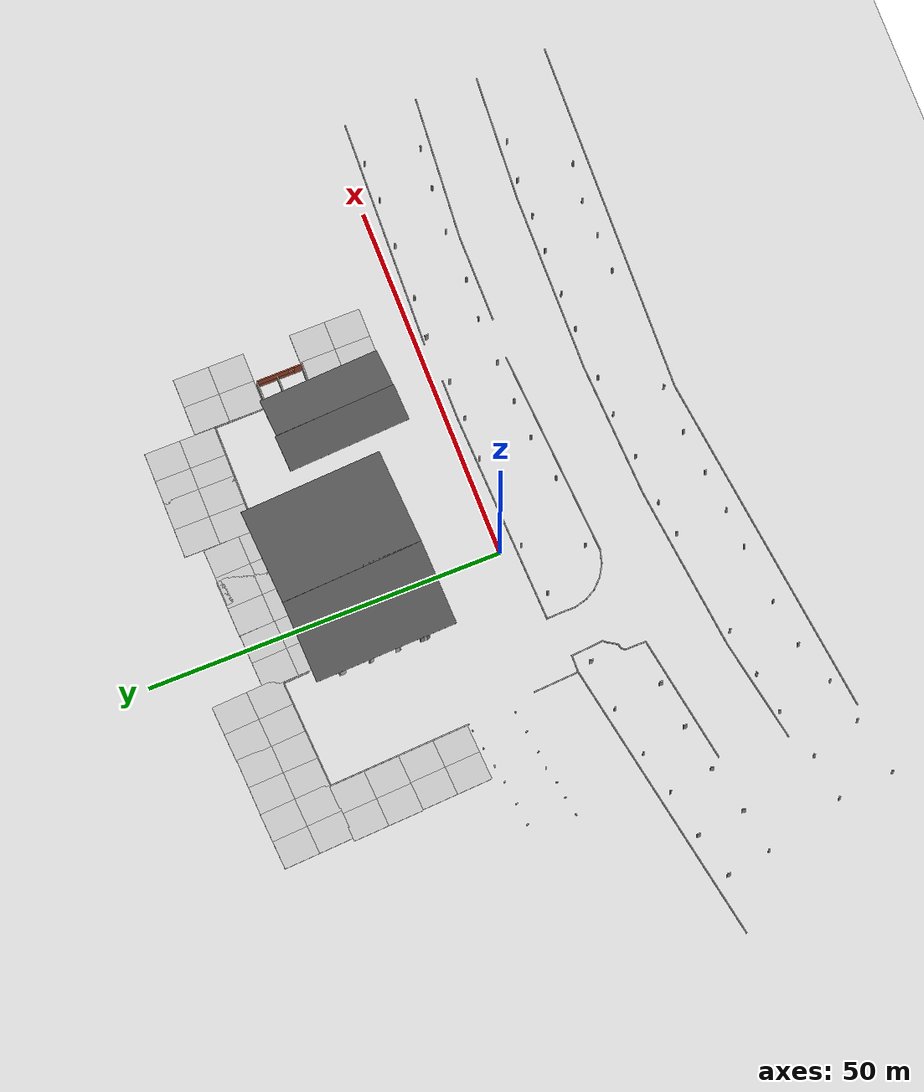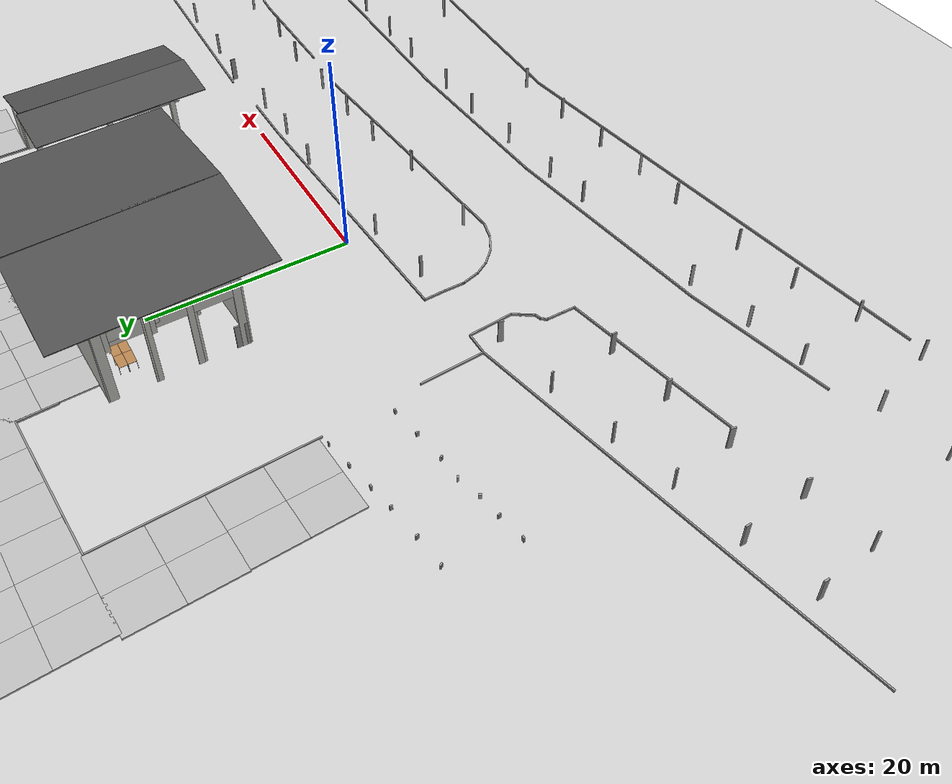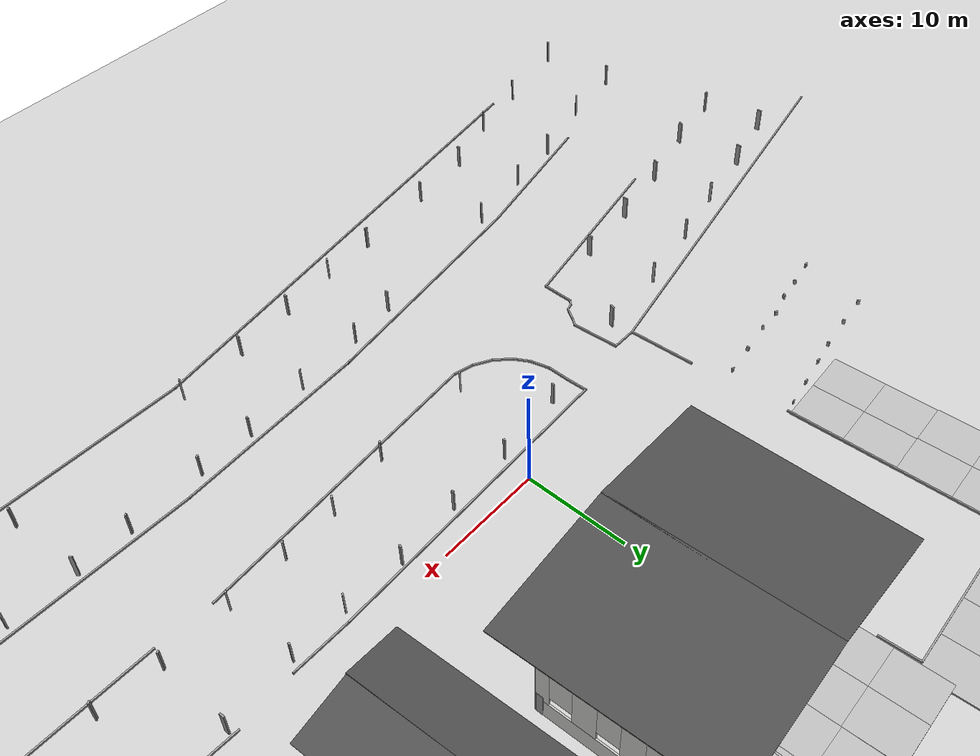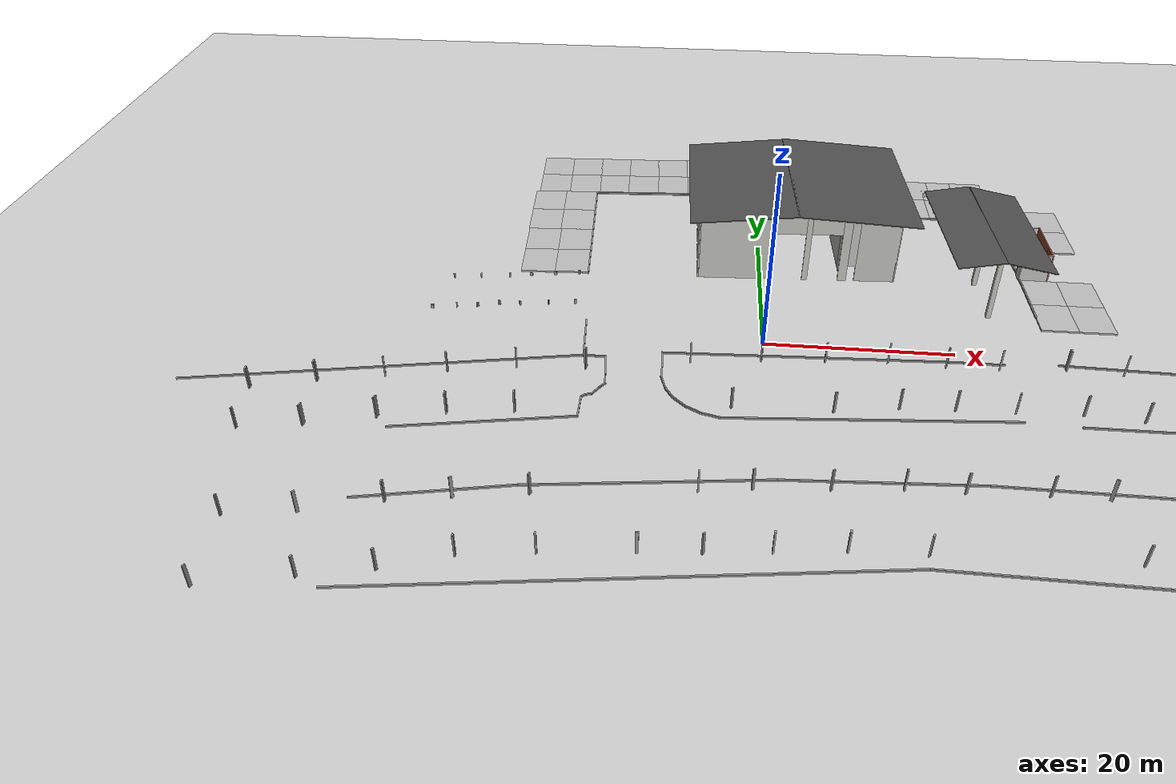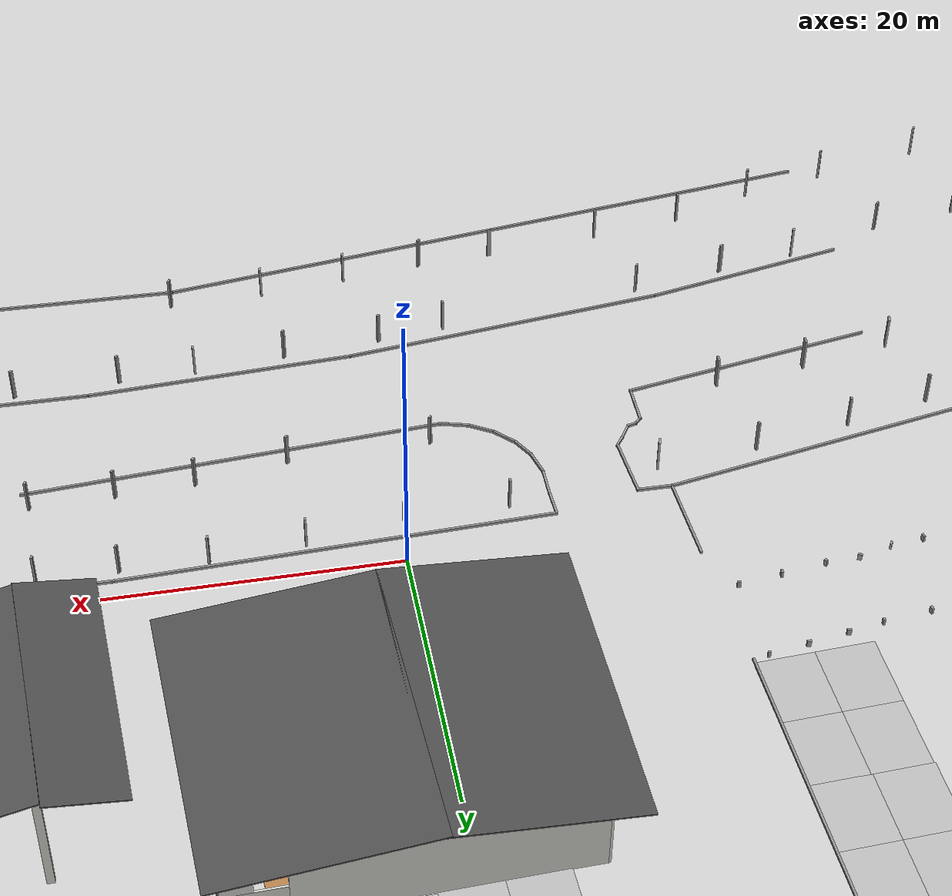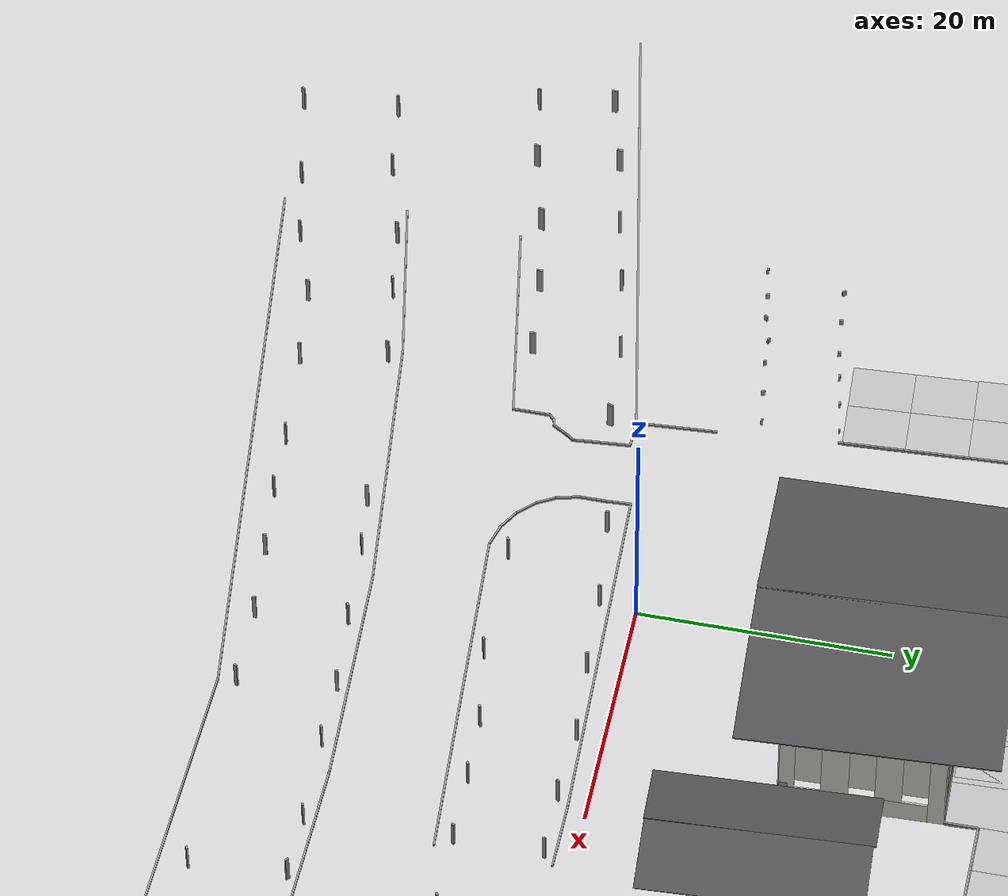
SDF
<sdf version="1.7">
 <world name="default">
  <light name="sun" type="directional">
   <pose>0 0 10 0 -0 0</pose>
   <diffuse>0.8 0.8 0.8 1</diffuse>
   <specular>0.2 0.2 0.2 1</specular>
   <attenuation>
    <range>1000</range>
    <constant>0.9</constant>
    <linear>0.01</linear>
    <quadratic>0.001</quadratic>
   </attenuation>
   <direction>-0.5 0.1 -0.9</direction>
   <spot><inner_angle>0</inner_angle><outer_angle>0</outer_angle><falloff>0</falloff></spot>
  </light>
  <model name="ground_plane">
   <static>1</static>
   <link name="link">
    <collision name="collision">
     <geometry><plane><normal>0 0 1</normal><size>100 100</size></plane></geometry>
     <surface><friction><ode><mu>100</mu><mu2>50</mu2></ode></friction></surface>
    </collision>
    <visual name="visual">
     <cast_shadows>0</cast_shadows>
     <geometry><plane><normal>0 0 1</normal><size>100 100</size></plane></geometry>
     <material>
      <script><uri>file://media/materials/scripts/gazebo.material</uri><name>Gazebo/Grey</name></script>
     </material>
    </visual>
   </link>
  </model>
  <gravity>0 0 -9.8</gravity>
  <magnetic_field>6e-06 2.3e-05 -4.2e-05</magnetic_field>
  <atmosphere type="adiabatic"/>
  <physics type="ode">
   <max_step_size>0.001</max_step_size>
   <real_time_factor>1</real_time_factor>
   <real_time_update_rate>1000</real_time_update_rate>
  </physics>
  <scene><ambient>0.4 0.4 0.4 1</ambient><background>0.7 0.7 0.7 1</background><shadows>1</shadows></scene>
  <spherical_coordinates>
   <surface_model>EARTH_WGS84</surface_model>
   <latitude_deg>0</latitude_deg>
   <longitude_deg>0</longitude_deg>
   <elevation>0</elevation>
   <heading_deg>0</heading_deg>
  </spherical_coordinates>
  <model name="vehicle_test1">
   <pose>1.6419 -2.1357 0 0 -0 0</pose>
   <link name="Wall_0">
    <pose>13.4971 22.2982 0 0 -0 -1.53906</pose>
    <visual name="Wall_0_Visual_0">
     <pose>-5.69686 0 4.5 0 -0 0</pose>
     <geometry><box><size>1.36263 0.15 9</size></box></geometry>
     <material>
      <script><uri>file://media/materials/scripts/gazebo.material</uri><name>Gazebo/CeilingTiled</name></script>
      <ambient>1 1 1 1</ambient>
     </material>
     <meta><layer>0</layer></meta>
    </visual>
    <collision name="Wall_0_Collision_0">
     <geometry><box><size>1.36263 0.15 9</size></box></geometry>
     <pose>-5.69686 0 4.5 0 -0 0</pose>
    </collision>
    <visual name="Wall_0_Visual_1">
     <pose>0.681317 0 1 0 -0 0</pose>
     <geometry><box><size>11.3937 0.15 2</size></box></geometry>
     <material>
      <script><uri>file://media/materials/scripts/gazebo.material</uri><name>Gazebo/CeilingTiled</name></script>
      <ambient>1 1 1 1</ambient>
     </material>
     <meta><layer>0</layer></meta>
    </visual>
    <collision name="Wall_0_Collision_1">
     <geometry><box><size>11.3937 0.15 2</size></box></geometry>
     <pose>0.681317 0 1 0 -0 0</pose>
    </collision>
    <visual name="Wall_0_Visual_2">
     <pose>-1.99597 0 5.5 0 -0 0</pose>
     <geometry><box><size>2.03913 0.15 7</size></box></geometry>
     <material>
      <script><uri>file://media/materials/scripts/gazebo.material</uri><name>Gazebo/CeilingTiled</name></script>
      <ambient>1 1 1 1</ambient>
     </material>
     <meta><layer>0</layer></meta>
    </visual>
    <collision name="Wall_0_Collision_2">
     <geometry><box><size>2.03913 0.15 7</size></box></geometry>
     <pose>-1.99597 0 5.5 0 -0 0</pose>
    </collision>
    <visual name="Wall_0_Visual_3">
     <pose>2.07219 0 5.5 0 -0 0</pose>
     <geometry><box><size>2.09719 0.15 7</size></box></geometry>
     <material>
      <script><uri>file://media/materials/scripts/gazebo.material</uri><name>Gazebo/CeilingTiled</name></script>
      <ambient>1 1 1 1</ambient>
     </material>
     <meta><layer>0</layer></meta>
    </visual>
    <collision name="Wall_0_Collision_3">
     <geometry><box><size>2.09719 0.15 7</size></box></geometry>
     <pose>2.07219 0 5.5 0 -0 0</pose>
    </collision>
    <visual name="Wall_0_Visual_4">
     <pose>5.74948 0 5.5 0 -0 0</pose>
     <geometry><box><size>1.25739 0.15 7</size></box></geometry>
     <material>
      <script><uri>file://media/materials/scripts/gazebo.material</uri><name>Gazebo/CeilingTiled</name></script>
      <ambient>1 1 1 1</ambient>
     </material>
     <meta><layer>0</layer></meta>
    </visual>
    <collision name="Wall_0_Collision_4">
     <geometry><box><size>1.25739 0.15 7</size></box></geometry>
     <pose>5.74948 0 5.5 0 -0 0</pose>
    </collision>
    <visual name="Wall_0_Visual_5">
     <pose>-4.01554 0 6 0 -0 0</pose>
     <geometry><box><size>2 0.15 6</size></box></geometry>
     <material>
      <script><uri>file://media/materials/scripts/gazebo.material</uri><name>Gazebo/CeilingTiled</name></script>
      <ambient>1 1 1 1</ambient>
     </material>
     <meta><layer>0</layer></meta>
    </visual>
    <collision name="Wall_0_Collision_5">
     <geometry><box><size>2 0.15 6</size></box></geometry>
     <pose>-4.01554 0 6 0 -0 0</pose>
    </collision>
    <visual name="Wall_0_Visual_6">
     <pose>0.023594 0 6 0 -0 0</pose>
     <geometry><box><size>2 0.15 6</size></box></geometry>
     <material>
      <script><uri>file://media/materials/scripts/gazebo.material</uri><name>Gazebo/CeilingTiled</name></script>
      <ambient>1 1 1 1</ambient>
     </material>
     <meta><layer>0</layer></meta>
    </visual>
    <collision name="Wall_0_Collision_6">
     <geometry><box><size>2 0.15 6</size></box></geometry>
     <pose>0.023594 0 6 0 -0 0</pose>
    </collision>
    <visual name="Wall_0_Visual_7">
     <pose>4.12079 0 6 0 -0 0</pose>
     <geometry><box><size>2 0.15 6</size></box></geometry>
     <material>
      <script><uri>file://media/materials/scripts/gazebo.material</uri><name>Gazebo/CeilingTiled</name></script>
      <ambient>1 1 1 1</ambient>
     </material>
     <meta><layer>0</layer></meta>
    </visual>
    <collision name="Wall_0_Collision_7">
     <geometry><box><size>2 0.15 6</size></box></geometry>
     <pose>4.12079 0 6 0 -0 0</pose>
    </collision>
   </link>
   <link name="Wall_100">
    <collision name="Wall_100_Collision">
     <geometry><box><size>0.2 0.1 0.5</size></box></geometry>
     <pose>0 0 0.25 0 -0 0</pose>
    </collision>
    <visual name="Wall_100_Visual">
     <pose>0 0 0.25 0 -0 0</pose>
     <geometry><box><size>0.2 0.1 0.5</size></box></geometry>
     <material>
      <script><uri>file://media/materials/scripts/gazebo.material</uri><name>Gazebo/Grey</name></script>
      <ambient>1 1 1 1</ambient>
     </material>
     <meta><layer>0</layer></meta>
    </visual>
    <pose>-22.6696 14.2893 0 0 -0 0</pose>
   </link>
   <link name="Wall_105">
    <collision name="Wall_105_Collision">
     <geometry><box><size>0.25 0.15 0.5</size></box></geometry>
     <pose>0 0 0.25 0 -0 0</pose>
    </collision>
    <visual name="Wall_105_Visual">
     <pose>0 0 0.25 0 -0 0</pose>
     <geometry><box><size>0.25 0.15 0.5</size></box></geometry>
     <material>
      <script><uri>file://media/materials/scripts/gazebo.material</uri><name>Gazebo/Grey</name></script>
      <ambient>1 1 1 1</ambient>
     </material>
     <meta><layer>0</layer></meta>
    </visual>
    <pose>-22.3949 8.11717 0 0 -0 0</pose>
   </link>
   <link name="Wall_107">
    <collision name="Wall_107_Collision">
     <geometry><box><size>0.3 0.15 0.5</size></box></geometry>
     <pose>0 0 0.25 0 -0 0</pose>
    </collision>
    <visual name="Wall_107_Visual">
     <pose>0 0 0.25 0 -0 0</pose>
     <geometry><box><size>0.3 0.15 0.5</size></box></geometry>
     <material>
      <script><uri>file://media/materials/scripts/gazebo.material</uri><name>Gazebo/Grey</name></script>
      <ambient>1 1 1 1</ambient>
     </material>
     <meta><layer>0</layer></meta>
    </visual>
    <pose>-25.3879 13.8422 0 0 -0 3.14159</pose>
   </link>
   <link name="Wall_11">
    <collision name="Wall_11_Collision">
     <geometry><box><size>20.175 0.15 0.2</size></box></geometry>
     <pose>0 0 0.1 0 -0 0</pose>
    </collision>
    <visual name="Wall_11_Visual">
     <pose>0 0 0.1 0 -0 0</pose>
     <geometry><box><size>20.175 0.15 0.2</size></box></geometry>
     <material>
      <script><uri>file://media/materials/scripts/gazebo.material</uri><name>Gazebo/Grey</name></script>
      <ambient>1 1 1 1</ambient>
     </material>
     <meta><layer>0</layer></meta>
    </visual>
    <pose>-22.1369 24.4272 0 0 -0 -1.52084</pose>
   </link>
   <link name="Wall_110">
    <collision name="Wall_110_Collision">
     <geometry><box><size>0.3 0.15 0.5</size></box></geometry>
     <pose>0 0 0.25 0 -0 0</pose>
    </collision>
    <visual name="Wall_110_Visual">
     <pose>0 0 0.25 0 -0 0</pose>
     <geometry><box><size>0.3 0.15 0.5</size></box></geometry>
     <material>
      <script><uri>file://media/materials/scripts/gazebo.material</uri><name>Gazebo/Grey</name></script>
      <ambient>1 1 1 1</ambient>
     </material>
     <meta><layer>0</layer></meta>
    </visual>
    <pose>-25.3869 7.69017 0 0 -0 1.5708</pose>
   </link>
   <link name="Wall_112">
    <collision name="Wall_112_Collision">
     <geometry><box><size>0.3 0.15 0.5</size></box></geometry>
     <pose>0 0 0.25 0 -0 0</pose>
    </collision>
    <visual name="Wall_112_Visual">
     <pose>0 0 0.25 0 -0 0</pose>
     <geometry><box><size>0.3 0.15 0.5</size></box></geometry>
     <material>
      <script><uri>file://media/materials/scripts/gazebo.material</uri><name>Gazebo/Grey</name></script>
      <ambient>1 1 1 1</ambient>
     </material>
     <meta><layer>0</layer></meta>
    </visual>
    <pose>-28.1709 13.3492 0 0 -0 3.14159</pose>
   </link>
   <link name="Wall_114">
    <collision name="Wall_114_Collision">
     <geometry><box><size>0.25 0.15 0.5</size></box></geometry>
     <pose>0 0 0.25 0 -0 0</pose>
    </collision>
    <visual name="Wall_114_Visual">
     <pose>0 0 0.25 0 -0 0</pose>
     <geometry><box><size>0.25 0.15 0.5</size></box></geometry>
     <material>
      <script><uri>file://media/materials/scripts/gazebo.material</uri><name>Gazebo/Grey</name></script>
      <ambient>1 1 1 1</ambient>
     </material>
     <meta><layer>0</layer></meta>
    </visual>
    <pose>-28.4909 7.24367 0 0 -0 -1.04918</pose>
   </link>
   <link name="Wall_116">
    <collision name="Wall_116_Collision">
     <geometry><box><size>0.25 0.15 0.5</size></box></geometry>
     <pose>0 0 0.25 0 -0 0</pose>
    </collision>
    <visual name="Wall_116_Visual">
     <pose>0 0 0.25 0 -0 0</pose>
     <geometry><box><size>0.25 0.15 0.5</size></box></geometry>
     <material>
      <script><uri>file://media/materials/scripts/gazebo.material</uri><name>Gazebo/Grey</name></script>
      <ambient>1 1 1 1</ambient>
     </material>
     <meta><layer>0</layer></meta>
    </visual>
    <pose>-30.6149 12.8902 0 0 -0 1.5708</pose>
   </link>
   <link name="Wall_118">
    <collision name="Wall_118_Collision">
     <geometry><box><size>0.3 0.15 0.5</size></box></geometry>
     <pose>0 0 0.25 0 -0 0</pose>
    </collision>
    <visual name="Wall_118_Visual">
     <pose>0 0 0.25 0 -0 0</pose>
     <geometry><box><size>0.3 0.15 0.5</size></box></geometry>
     <material>
      <script><uri>file://media/materials/scripts/gazebo.material</uri><name>Gazebo/Grey</name></script>
      <ambient>1 1 1 1</ambient>
     </material>
     <meta><layer>0</layer></meta>
    </visual>
    <pose>-30.8439 7.13067 0 0 -0 2.61831</pose>
   </link>
   <link name="Wall_120">
    <collision name="Wall_120_Collision">
     <geometry><box><size>0.3 0.15 0.5</size></box></geometry>
     <pose>0 0 0.25 0 -0 0</pose>
    </collision>
    <visual name="Wall_120_Visual">
     <pose>0 0 0.25 0 -0 0</pose>
     <geometry><box><size>0.3 0.15 0.5</size></box></geometry>
     <material>
      <script><uri>file://media/materials/scripts/gazebo.material</uri><name>Gazebo/Grey</name></script>
      <ambient>1 1 1 1</ambient>
     </material>
     <meta><layer>0</layer></meta>
    </visual>
    <pose>-33.9314 12.4717 0 0 -0 1.83354</pose>
   </link>
   <link name="Wall_122">
    <collision name="Wall_122_Collision">
     <geometry><box><size>0.3 0.15 0.5</size></box></geometry>
     <pose>0 0 0.25 0 -0 0</pose>
    </collision>
    <visual name="Wall_122_Visual">
     <pose>0 0 0.25 0 -0 0</pose>
     <geometry><box><size>0.3 0.15 0.5</size></box></geometry>
     <material>
      <script><uri>file://media/materials/scripts/gazebo.material</uri><name>Gazebo/Grey</name></script>
      <ambient>1 1 1 1</ambient>
     </material>
     <meta><layer>0</layer></meta>
    </visual>
    <pose>-33.1654 6.48417 0 0 -0 1.04752</pose>
   </link>
   <link name="Wall_124">
    <collision name="Wall_124_Collision">
     <geometry><box><size>0.3 0.15 0.5</size></box></geometry>
     <pose>0 0 0.25 0 -0 0</pose>
    </collision>
    <visual name="Wall_124_Visual">
     <pose>0 0 0.25 0 -0 0</pose>
     <geometry><box><size>0.3 0.15 0.5</size></box></geometry>
     <material>
      <script><uri>file://media/materials/scripts/gazebo.material</uri><name>Gazebo/Grey</name></script>
      <ambient>1 1 1 1</ambient>
     </material>
     <meta><layer>0</layer></meta>
    </visual>
    <pose>-37.0254 12.1672 0 0 -0 2.09408</pose>
   </link>
   <link name="Wall_126">
    <collision name="Wall_126_Collision">
     <geometry><box><size>0.3 0.15 0.5</size></box></geometry>
     <pose>0 0 0.25 0 -0 0</pose>
    </collision>
    <visual name="Wall_126_Visual">
     <pose>0 0 0.25 0 -0 0</pose>
     <geometry><box><size>0.3 0.15 0.5</size></box></geometry>
     <material>
      <script><uri>file://media/materials/scripts/gazebo.material</uri><name>Gazebo/Grey</name></script>
      <ambient>1 1 1 1</ambient>
     </material>
     <meta><layer>0</layer></meta>
    </visual>
    <pose>-35.4674 6.19667 0 0 -0 1.83354</pose>
   </link>
   <link name="Wall_128">
    <collision name="Wall_128_Collision">
     <geometry><box><size>0.3 0.15 0.5</size></box></geometry>
     <pose>0 0 0.25 0 -0 0</pose>
    </collision>
    <visual name="Wall_128_Visual">
     <pose>0 0 0.25 0 -0 0</pose>
     <geometry><box><size>0.3 0.15 0.5</size></box></geometry>
     <material>
      <script><uri>file://media/materials/scripts/gazebo.material</uri><name>Gazebo/Grey</name></script>
      <ambient>1 1 1 1</ambient>
     </material>
     <meta><layer>0</layer></meta>
    </visual>
    <pose>-38.1379 5.72617 0 0 -0 3.14159</pose>
   </link>
   <link name="Wall_13">
    <collision name="Wall_13_Collision">
     <geometry><box><size>3.75555 0.15 0.2</size></box></geometry>
     <pose>0 0 0.1 0 -0 0</pose>
    </collision>
    <visual name="Wall_13_Visual">
     <pose>0 0 0.1 0 -0 0</pose>
     <geometry><box><size>3.75555 0.15 0.2</size></box></geometry>
     <material>
      <script><uri>file://media/materials/scripts/gazebo.material</uri><name>Gazebo/Grey</name></script>
      <ambient>1 1 1 1</ambient>
     </material>
     <meta><layer>0</layer></meta>
    </visual>
    <pose>-7.4369 33.4272 0 0 -0 -1.5153</pose>
   </link>
   <link name="Wall_132">
    <collision name="Wall_132_Collision">
     <geometry><box><size>21.3 0.15 0.2</size></box></geometry>
     <pose>0 0 0.1 0 -0 0</pose>
    </collision>
    <visual name="Wall_132_Visual">
     <pose>0 0 0.1 0 -0 0</pose>
     <geometry><box><size>21.3 0.15 0.2</size></box></geometry>
     <material>
      <script><uri>file://media/materials/scripts/gazebo.material</uri><name>Gazebo/Grey</name></script>
      <ambient>1 1 1 1</ambient>
     </material>
     <meta><layer>0</layer></meta>
    </visual>
    <pose>28.2981 20.4482 0 0 -0 -1.56134</pose>
   </link>
   <link name="Wall_134">
    <collision name="Wall_134_Collision">
     <geometry><box><size>0.5 0.15 2.5</size></box></geometry>
     <pose>0 0 1.25 0 -0 0</pose>
    </collision>
    <visual name="Wall_134_Visual">
     <pose>0 0 1.25 0 -0 0</pose>
     <geometry><box><size>0.5 0.15 2.5</size></box></geometry>
     <material>
      <script><uri>file://media/materials/scripts/gazebo.material</uri><name>Gazebo/Grey</name></script>
      <ambient>1 1 1 1</ambient>
     </material>
     <meta><layer>0</layer></meta>
    </visual>
    <pose>-53.0952 -9.91699 0 0 -0 -1.5708</pose>
   </link>
   <link name="Wall_136">
    <collision name="Wall_136_Collision">
     <geometry><box><size>0.5 0.15 2.5</size></box></geometry>
     <pose>0 0 1.25 0 -0 0</pose>
    </collision>
    <visual name="Wall_136_Visual">
     <pose>0 0 1.25 0 -0 0</pose>
     <geometry><box><size>0.5 0.15 2.5</size></box></geometry>
     <material>
      <script><uri>file://media/materials/scripts/gazebo.material</uri><name>Gazebo/Grey</name></script>
      <ambient>1 1 1 1</ambient>
     </material>
     <meta><layer>0</layer></meta>
    </visual>
    <pose>-46.7288 -8.20296 0 0 -0 -1.5708</pose>
   </link>
   <link name="Wall_138">
    <collision name="Wall_138_Collision">
     <geometry><box><size>0.25 0.15 2.5</size></box></geometry>
     <pose>0 0 1.25 0 -0 0</pose>
    </collision>
    <visual name="Wall_138_Visual">
     <pose>0 0 1.25 0 -0 0</pose>
     <geometry><box><size>0.25 0.15 2.5</size></box></geometry>
     <material>
      <script><uri>file://media/materials/scripts/gazebo.material</uri><name>Gazebo/Grey</name></script>
      <ambient>1 1 1 1</ambient>
     </material>
     <meta><layer>0</layer></meta>
    </visual>
    <pose>-40.0347 -6.88693 0 0 -0 -1.309</pose>
   </link>
   <link name="Wall_140">
    <collision name="Wall_140_Collision">
     <geometry><box><size>0.25 0.15 2.5</size></box></geometry>
     <pose>0 0 1.25 0 -0 0</pose>
    </collision>
    <visual name="Wall_140_Visual">
     <pose>0 0 1.25 0 -0 0</pose>
     <geometry><box><size>0.25 0.15 2.5</size></box></geometry>
     <material>
      <script><uri>file://media/materials/scripts/gazebo.material</uri><name>Gazebo/Grey</name></script>
      <ambient>1 1 1 1</ambient>
     </material>
     <meta><layer>0</layer></meta>
    </visual>
    <pose>-33.9261 -5.48943 0 0 -0 -1.5708</pose>
   </link>
   <link name="Wall_142">
    <collision name="Wall_142_Collision">
     <geometry><box><size>0.25 0.15 2.5</size></box></geometry>
     <pose>0 0 1.25 0 -0 0</pose>
    </collision>
    <visual name="Wall_142_Visual">
     <pose>0 0 1.25 0 -0 0</pose>
     <geometry><box><size>0.25 0.15 2.5</size></box></geometry>
     <material>
      <script><uri>file://media/materials/scripts/gazebo.material</uri><name>Gazebo/Grey</name></script>
      <ambient>1 1 1 1</ambient>
     </material>
     <meta><layer>0</layer></meta>
    </visual>
    <pose>-26.9871 -4.19346 0 0 -0 -1.309</pose>
   </link>
   <link name="Wall_144">
    <collision name="Wall_144_Collision">
     <geometry><box><size>0.5 0.15 2.5</size></box></geometry>
     <pose>0 0 1.25 0 -0 0</pose>
    </collision>
    <visual name="Wall_144_Visual">
     <pose>0 0 1.25 0 -0 0</pose>
     <geometry><box><size>0.5 0.15 2.5</size></box></geometry>
     <material>
      <script><uri>file://media/materials/scripts/gazebo.material</uri><name>Gazebo/Grey</name></script>
      <ambient>1 1 1 1</ambient>
     </material>
     <meta><layer>0</layer></meta>
    </visual>
    <pose>-19.8744 -3.6146 0 0 -0 -1.8326</pose>
   </link>
   <link name="Wall_146">
    <collision name="Wall_146_Collision">
     <geometry><box><size>0.5 0.15 2.5</size></box></geometry>
     <pose>0 0 1.25 0 -0 0</pose>
    </collision>
    <visual name="Wall_146_Visual">
     <pose>0 0 1.25 0 -0 0</pose>
     <geometry><box><size>0.5 0.15 2.5</size></box></geometry>
     <material>
      <script><uri>file://media/materials/scripts/gazebo.material</uri><name>Gazebo/Grey</name></script>
      <ambient>1 1 1 1</ambient>
     </material>
     <meta><layer>0</layer></meta>
    </visual>
    <pose>-25.9856 -11.1413 0 0 -0 -1.5708</pose>
   </link>
   <link name="Wall_148">
    <collision name="Wall_148_Collision">
     <geometry><box><size>0.5 0.15 2.5</size></box></geometry>
     <pose>0 0 1.25 0 -0 0</pose>
    </collision>
    <visual name="Wall_148_Visual">
     <pose>0 0 1.25 0 -0 0</pose>
     <geometry><box><size>0.5 0.15 2.5</size></box></geometry>
     <material>
      <script><uri>file://media/materials/scripts/gazebo.material</uri><name>Gazebo/Grey</name></script>
      <ambient>1 1 1 1</ambient>
     </material>
     <meta><layer>0</layer></meta>
    </visual>
    <pose>-32.5619 -11.9458 0 0 -0 -1.5708</pose>
   </link>
   <link name="Wall_15">
    <collision name="Wall_15_Collision">
     <geometry><box><size>6.5368 0.15 0.2</size></box></geometry>
     <pose>0 0 0.1 0 -0 0</pose>
    </collision>
    <visual name="Wall_15_Visual">
     <pose>0 0 0.1 0 -0 0</pose>
     <geometry><box><size>6.5368 0.15 0.2</size></box></geometry>
     <material>
      <script><uri>file://media/materials/scripts/gazebo.material</uri><name>Gazebo/Grey</name></script>
      <ambient>1 1 1 1</ambient>
     </material>
     <meta><layer>0</layer></meta>
    </visual>
    <pose>-20.5699 1.58267 0 0 -0 -1.51001</pose>
   </link>
   <link name="Wall_150">
    <collision name="Wall_150_Collision">
     <geometry><box><size>0.5 0.15 2.5</size></box></geometry>
     <pose>0 0 1.25 0 -0 0</pose>
    </collision>
    <visual name="Wall_150_Visual">
     <pose>0 0 1.25 0 -0 0</pose>
     <geometry><box><size>0.5 0.15 2.5</size></box></geometry>
     <material>
      <script><uri>file://media/materials/scripts/gazebo.material</uri><name>Gazebo/Grey</name></script>
      <ambient>1 1 1 1</ambient>
     </material>
     <meta><layer>0</layer></meta>
    </visual>
    <pose>-39.1135 -13.1642 0 0 -0 -1.8326</pose>
   </link>
   <link name="Wall_152">
    <collision name="Wall_152_Collision">
     <geometry><box><size>0.5 0.15 2.5</size></box></geometry>
     <pose>0 0 1.25 0 -0 0</pose>
    </collision>
    <visual name="Wall_152_Visual">
     <pose>0 0 1.25 0 -0 0</pose>
     <geometry><box><size>0.5 0.15 2.5</size></box></geometry>
     <material>
      <script><uri>file://media/materials/scripts/gazebo.material</uri><name>Gazebo/Grey</name></script>
      <ambient>1 1 1 1</ambient>
     </material>
     <meta><layer>0</layer></meta>
    </visual>
    <pose>-45.8646 -14.9482 0 0 -0 -1.8326</pose>
   </link>
   <link name="Wall_154">
    <collision name="Wall_154_Collision">
     <geometry><box><size>0.25 0.15 2.5</size></box></geometry>
     <pose>0 0 1.25 0 -0 0</pose>
    </collision>
    <visual name="Wall_154_Visual">
     <pose>0 0 1.25 0 -0 0</pose>
     <geometry><box><size>0.25 0.15 2.5</size></box></geometry>
     <material>
      <script><uri>file://media/materials/scripts/gazebo.material</uri><name>Gazebo/Grey</name></script>
      <ambient>1 1 1 1</ambient>
     </material>
     <meta><layer>0</layer></meta>
    </visual>
    <pose>-52.0587 -16.0517 0 0 -0 -1.8326</pose>
   </link>
   <link name="Wall_156">
    <collision name="Wall_156_Collision">
     <geometry><box><size>0.3 0.15 2.5</size></box></geometry>
     <pose>0 0 1.25 0 -0 0</pose>
    </collision>
    <visual name="Wall_156_Visual">
     <pose>0 0 1.25 0 -0 0</pose>
     <geometry><box><size>0.3 0.15 2.5</size></box></geometry>
     <material>
      <script><uri>file://media/materials/scripts/gazebo.material</uri><name>Gazebo/Grey</name></script>
      <ambient>1 1 1 1</ambient>
     </material>
     <meta><layer>0</layer></meta>
    </visual>
    <pose>-9.19513 -1.69152 0 0 -0 1.5708</pose>
   </link>
   <link name="Wall_158">
    <collision name="Wall_158_Collision">
     <geometry><box><size>0.25 0.15 2.5</size></box></geometry>
     <pose>0 0 1.25 0 -0 0</pose>
    </collision>
    <visual name="Wall_158_Visual">
     <pose>0 0 1.25 0 -0 0</pose>
     <geometry><box><size>0.25 0.15 2.5</size></box></geometry>
     <material>
      <script><uri>file://media/materials/scripts/gazebo.material</uri><name>Gazebo/Grey</name></script>
      <ambient>1 1 1 1</ambient>
     </material>
     <meta><layer>0</layer></meta>
    </visual>
    <pose>-1.89723 -0.800389 0 0 -0 -1.8326</pose>
   </link>
   <link name="Wall_160">
    <collision name="Wall_160_Collision">
     <geometry><box><size>0.25 0.15 2.5</size></box></geometry>
     <pose>0 0 1.25 0 -0 0</pose>
    </collision>
    <visual name="Wall_160_Visual">
     <pose>0 0 1.25 0 -0 0</pose>
     <geometry><box><size>0.25 0.15 2.5</size></box></geometry>
     <material>
      <script><uri>file://media/materials/scripts/gazebo.material</uri><name>Gazebo/Grey</name></script>
      <ambient>1 1 1 1</ambient>
     </material>
     <meta><layer>0</layer></meta>
    </visual>
    <pose>4.69198 -0.452291 0 0 -0 -1.5708</pose>
   </link>
   <link name="Wall_162">
    <collision name="Wall_162_Collision">
     <geometry><box><size>0.3 0.15 2.5</size></box></geometry>
     <pose>0 0 1.25 0 -0 0</pose>
    </collision>
    <visual name="Wall_162_Visual">
     <pose>0 0 1.25 0 -0 0</pose>
     <geometry><box><size>0.3 0.15 2.5</size></box></geometry>
     <material>
      <script><uri>file://media/materials/scripts/gazebo.material</uri><name>Gazebo/Grey</name></script>
      <ambient>1 1 1 1</ambient>
     </material>
     <meta><layer>0</layer></meta>
    </visual>
    <pose>11.1477 0.054935 0 0 -0 1.309</pose>
   </link>
   <link name="Wall_164">
    <collision name="Wall_164_Collision">
     <geometry><box><size>0.25 0.15 2.5</size></box></geometry>
     <pose>0 0 1.25 0 -0 0</pose>
    </collision>
    <visual name="Wall_164_Visual">
     <pose>0 0 1.25 0 -0 0</pose>
     <geometry><box><size>0.25 0.15 2.5</size></box></geometry>
     <material>
      <script><uri>file://media/materials/scripts/gazebo.material</uri><name>Gazebo/Grey</name></script>
      <ambient>1 1 1 1</ambient>
     </material>
     <meta><layer>0</layer></meta>
    </visual>
    <pose>17.015 -0.165752 0 0 -0 -2.0944</pose>
   </link>
   <link name="Wall_166">
    <collision name="Wall_166_Collision">
     <geometry><box><size>0.25 0.15 2.5</size></box></geometry>
     <pose>0 0 1.25 0 -0 0</pose>
    </collision>
    <visual name="Wall_166_Visual">
     <pose>0 0 1.25 0 -0 0</pose>
     <geometry><box><size>0.25 0.15 2.5</size></box></geometry>
     <material>
      <script><uri>file://media/materials/scripts/gazebo.material</uri><name>Gazebo/Grey</name></script>
      <ambient>1 1 1 1</ambient>
     </material>
     <meta><layer>0</layer></meta>
    </visual>
    <pose>22.414 -0.100786 0 0 -0 -1.8326</pose>
   </link>
   <link name="Wall_168">
    <collision name="Wall_168_Collision">
     <geometry><box><size>0.25 0.15 2.5</size></box></geometry>
     <pose>0 0 1.25 0 -0 0</pose>
    </collision>
    <visual name="Wall_168_Visual">
     <pose>0 0 1.25 0 -0 0</pose>
     <geometry><box><size>0.25 0.15 2.5</size></box></geometry>
     <material>
      <script><uri>file://media/materials/scripts/gazebo.material</uri><name>Gazebo/Grey</name></script>
      <ambient>1 1 1 1</ambient>
     </material>
     <meta><layer>0</layer></meta>
    </visual>
    <pose>-4.99789 -8.69296 0 0 -0 -2.35619</pose>
   </link>
   <link name="Wall_17">
    <collision name="Wall_17_Collision">
     <geometry><box><size>41.4472 0.15 0.2</size></box></geometry>
     <pose>0 0 0.1 0 -0 0</pose>
    </collision>
    <visual name="Wall_17_Visual">
     <pose>0 0 0.1 0 -0 0</pose>
     <geometry><box><size>41.4472 0.15 0.2</size></box></geometry>
     <material>
      <script><uri>file://media/materials/scripts/gazebo.material</uri><name>Gazebo/Grey</name></script>
      <ambient>1 1 1 1</ambient>
     </material>
     <meta><layer>0</layer></meta>
    </visual>
    <pose>-40.6609 -5.46283 0 0 -0 -2.95365</pose>
   </link>
   <link name="Wall_170">
    <collision name="Wall_170_Collision">
     <geometry><box><size>0.25 0.15 2.5</size></box></geometry>
     <pose>0 0 1.25 0 -0 0</pose>
    </collision>
    <visual name="Wall_170_Visual">
     <pose>0 0 1.25 0 -0 0</pose>
     <geometry><box><size>0.25 0.15 2.5</size></box></geometry>
     <material>
      <script><uri>file://media/materials/scripts/gazebo.material</uri><name>Gazebo/Grey</name></script>
      <ambient>1 1 1 1</ambient>
     </material>
     <meta><layer>0</layer></meta>
    </visual>
    <pose>4.92852 -8.47272 0 0 -0 -2.61799</pose>
   </link>
   <link name="Wall_172">
    <collision name="Wall_172_Collision">
     <geometry><box><size>0.25 0.15 2.5</size></box></geometry>
     <pose>0 0 1.25 0 -0 0</pose>
    </collision>
    <visual name="Wall_172_Visual">
     <pose>0 0 1.25 0 -0 0</pose>
     <geometry><box><size>0.25 0.15 2.5</size></box></geometry>
     <material>
      <script><uri>file://media/materials/scripts/gazebo.material</uri><name>Gazebo/Grey</name></script>
      <ambient>1 1 1 1</ambient>
     </material>
     <meta><layer>0</layer></meta>
    </visual>
    <pose>11.3378 -7.39869 0 0 -0 -2.35619</pose>
   </link>
   <link name="Wall_174">
    <collision name="Wall_174_Collision">
     <geometry><box><size>0.25 0.15 2.5</size></box></geometry>
     <pose>0 0 1.25 0 -0 0</pose>
    </collision>
    <visual name="Wall_174_Visual">
     <pose>0 0 1.25 0 -0 0</pose>
     <geometry><box><size>0.25 0.15 2.5</size></box></geometry>
     <material>
      <script><uri>file://media/materials/scripts/gazebo.material</uri><name>Gazebo/Grey</name></script>
      <ambient>1 1 1 1</ambient>
     </material>
     <meta><layer>0</layer></meta>
    </visual>
    <pose>16.7597 -7.15383 0 0 -0 -2.35619</pose>
   </link>
   <link name="Wall_176">
    <collision name="Wall_176_Collision">
     <geometry><box><size>0.25 0.15 2.5</size></box></geometry>
     <pose>0 0 1.25 0 -0 0</pose>
    </collision>
    <visual name="Wall_176_Visual">
     <pose>0 0 1.25 0 -0 0</pose>
     <geometry><box><size>0.25 0.15 2.5</size></box></geometry>
     <material>
      <script><uri>file://media/materials/scripts/gazebo.material</uri><name>Gazebo/Grey</name></script>
      <ambient>1 1 1 1</ambient>
     </material>
     <meta><layer>0</layer></meta>
    </visual>
    <pose>22.5418 -7.02186 0 0 -0 -2.0944</pose>
   </link>
   <link name="Wall_178">
    <collision name="Wall_178_Collision">
     <geometry><box><size>0.5 0.15 2.5</size></box></geometry>
     <pose>0 0 1.25 0 -0 0</pose>
    </collision>
    <visual name="Wall_178_Visual">
     <pose>0 0 1.25 0 -0 0</pose>
     <geometry><box><size>0.5 0.15 2.5</size></box></geometry>
     <material>
      <script><uri>file://media/materials/scripts/gazebo.material</uri><name>Gazebo/Grey</name></script>
      <ambient>1 1 1 1</ambient>
     </material>
     <meta><layer>0</layer></meta>
    </visual>
    <pose>29.2332 0.549836 0 0 -0 -1.5708</pose>
   </link>
   <link name="Wall_180">
    <collision name="Wall_180_Collision">
     <geometry><box><size>0.25 0.15 2.5</size></box></geometry>
     <pose>0 0 1.25 0 -0 0</pose>
    </collision>
    <visual name="Wall_180_Visual">
     <pose>0 0 1.25 0 -0 0</pose>
     <geometry><box><size>0.25 0.15 2.5</size></box></geometry>
     <material>
      <script><uri>file://media/materials/scripts/gazebo.material</uri><name>Gazebo/Grey</name></script>
      <ambient>1 1 1 1</ambient>
     </material>
     <meta><layer>0</layer></meta>
    </visual>
    <pose>34.8421 0.099635 0 0 -0 -2.0944</pose>
   </link>
   <link name="Wall_182">
    <collision name="Wall_182_Collision">
     <geometry><box><size>0.25 0.15 2.5</size></box></geometry>
     <pose>0 0 1.25 0 -0 0</pose>
    </collision>
    <visual name="Wall_182_Visual">
     <pose>0 0 1.25 0 -0 0</pose>
     <geometry><box><size>0.25 0.15 2.5</size></box></geometry>
     <material>
      <script><uri>file://media/materials/scripts/gazebo.material</uri><name>Gazebo/Grey</name></script>
      <ambient>1 1 1 1</ambient>
     </material>
     <meta><layer>0</layer></meta>
    </visual>
    <pose>42.4717 -0.11696 0 0 -0 -1.8326</pose>
   </link>
   <link name="Wall_184">
    <collision name="Wall_184_Collision">
     <geometry><box><size>0.25 0.15 2.5</size></box></geometry>
     <pose>0 0 1.25 0 -0 0</pose>
    </collision>
    <visual name="Wall_184_Visual">
     <pose>0 0 1.25 0 -0 0</pose>
     <geometry><box><size>0.25 0.15 2.5</size></box></geometry>
     <material>
      <script><uri>file://media/materials/scripts/gazebo.material</uri><name>Gazebo/Grey</name></script>
      <ambient>1 1 1 1</ambient>
     </material>
     <meta><layer>0</layer></meta>
    </visual>
    <pose>49.1068 -0.490414 0 0 -0 -2.61799</pose>
   </link>
   <link name="Wall_186">
    <collision name="Wall_186_Collision">
     <geometry><box><size>0.25 0.15 2.5</size></box></geometry>
     <pose>0 0 1.25 0 -0 0</pose>
    </collision>
    <visual name="Wall_186_Visual">
     <pose>0 0 1.25 0 -0 0</pose>
     <geometry><box><size>0.25 0.15 2.5</size></box></geometry>
     <material>
      <script><uri>file://media/materials/scripts/gazebo.material</uri><name>Gazebo/Grey</name></script>
      <ambient>1 1 1 1</ambient>
     </material>
     <meta><layer>0</layer></meta>
    </visual>
    <pose>54.5899 -0.447869 0 0 -0 -2.35619</pose>
   </link>
   <link name="Wall_188">
    <collision name="Wall_188_Collision">
     <geometry><box><size>0.25 0.15 2.5</size></box></geometry>
     <pose>0 0 1.25 0 -0 0</pose>
    </collision>
    <visual name="Wall_188_Visual">
     <pose>0 0 1.25 0 -0 0</pose>
     <geometry><box><size>0.25 0.15 2.5</size></box></geometry>
     <material>
      <script><uri>file://media/materials/scripts/gazebo.material</uri><name>Gazebo/Grey</name></script>
      <ambient>1 1 1 1</ambient>
     </material>
     <meta><layer>0</layer></meta>
    </visual>
    <pose>53.8228 -8.22417 0 0 -0 -2.35619</pose>
   </link>
   <link name="Wall_19">
    <collision name="Wall_19_Collision">
     <geometry><box><size>1.5 0.15 0.2</size></box></geometry>
     <pose>0 0 0.1 0 -0 0</pose>
    </collision>
    <visual name="Wall_19_Visual">
     <pose>0 0 0.1 0 -0 0</pose>
     <geometry><box><size>1.5 0.15 0.2</size></box></geometry>
     <material>
      <script><uri>file://media/materials/scripts/gazebo.material</uri><name>Gazebo/Grey</name></script>
      <ambient>1 1 1 1</ambient>
     </material>
     <meta><layer>0</layer></meta>
    </visual>
    <pose>-19.8299 -10.7698 0 0 -0 -1.5708</pose>
   </link>
   <link name="Wall_190">
    <collision name="Wall_190_Collision">
     <geometry><box><size>0.25 0.15 2.5</size></box></geometry>
     <pose>0 0 1.25 0 -0 0</pose>
    </collision>
    <visual name="Wall_190_Visual">
     <pose>0 0 1.25 0 -0 0</pose>
     <geometry><box><size>0.25 0.15 2.5</size></box></geometry>
     <material>
      <script><uri>file://media/materials/scripts/gazebo.material</uri><name>Gazebo/Grey</name></script>
      <ambient>1 1 1 1</ambient>
     </material>
     <meta><layer>0</layer></meta>
    </visual>
    <pose>48.1281 -7.65836 0 0 -0 -2.61799</pose>
   </link>
   <link name="Wall_192">
    <collision name="Wall_192_Collision">
     <geometry><box><size>0.25 0.15 2.5</size></box></geometry>
     <pose>0 0 1.25 0 -0 0</pose>
    </collision>
    <visual name="Wall_192_Visual">
     <pose>0 0 1.25 0 -0 0</pose>
     <geometry><box><size>0.25 0.15 2.5</size></box></geometry>
     <material>
      <script><uri>file://media/materials/scripts/gazebo.material</uri><name>Gazebo/Grey</name></script>
      <ambient>1 1 1 1</ambient>
     </material>
     <meta><layer>0</layer></meta>
    </visual>
    <pose>41.7984 -7.14766 0 0 -0 -2.0944</pose>
   </link>
   <link name="Wall_194">
    <collision name="Wall_194_Collision">
     <geometry><box><size>0.25 0.15 2.5</size></box></geometry>
     <pose>0 0 1.25 0 -0 0</pose>
    </collision>
    <visual name="Wall_194_Visual">
     <pose>0 0 1.25 0 -0 0</pose>
     <geometry><box><size>0.25 0.15 2.5</size></box></geometry>
     <material>
      <script><uri>file://media/materials/scripts/gazebo.material</uri><name>Gazebo/Grey</name></script>
      <ambient>1 1 1 1</ambient>
     </material>
     <meta><layer>0</layer></meta>
    </visual>
    <pose>34.6386 -7.31451 0 0 -0 -2.61799</pose>
   </link>
   <link name="Wall_196">
    <collision name="Wall_196_Collision">
     <geometry><box><size>0.25 0.15 2.5</size></box></geometry>
     <pose>0 0 1.25 0 -0 0</pose>
    </collision>
    <visual name="Wall_196_Visual">
     <pose>0 0 1.25 0 -0 0</pose>
     <geometry><box><size>0.25 0.15 2.5</size></box></geometry>
     <material>
      <script><uri>file://media/materials/scripts/gazebo.material</uri><name>Gazebo/Grey</name></script>
      <ambient>1 1 1 1</ambient>
     </material>
     <meta><layer>0</layer></meta>
    </visual>
    <pose>29.0048 -6.81196 0 0 -0 -2.61799</pose>
   </link>
   <link name="Wall_198">
    <collision name="Wall_198_Collision">
     <geometry><box><size>0.25 0.15 2.5</size></box></geometry>
     <pose>0 0 1.25 0 -0 0</pose>
    </collision>
    <visual name="Wall_198_Visual">
     <pose>0 0 1.25 0 -0 0</pose>
     <geometry><box><size>0.25 0.15 2.5</size></box></geometry>
     <material>
      <script><uri>file://media/materials/scripts/gazebo.material</uri><name>Gazebo/Grey</name></script>
      <ambient>1 1 1 1</ambient>
     </material>
     <meta><layer>0</layer></meta>
    </visual>
    <pose>50.4794 -19.3711 0 0 -0 -1.8326</pose>
   </link>
   <link name="Wall_20">
    <collision name="Wall_20_Collision">
     <geometry><box><size>18.4012 0.15 0.2</size></box></geometry>
     <pose>0 0 0.1 0 -0 0</pose>
    </collision>
    <visual name="Wall_20_Visual">
     <pose>0 0 0.1 0 -0 0</pose>
     <geometry><box><size>18.4012 0.15 0.2</size></box></geometry>
     <material>
      <script><uri>file://media/materials/scripts/gazebo.material</uri><name>Gazebo/Grey</name></script>
      <ambient>1 1 1 1</ambient>
     </material>
     <meta><layer>0</layer></meta>
    </visual>
    <pose>-28.8129 -13.0518 0 0 -0 -2.96457</pose>
   </link>
   <link name="Wall_200">
    <collision name="Wall_200_Collision">
     <geometry><box><size>0.3 0.15 2.5</size></box></geometry>
     <pose>0 0 1.25 0 -0 0</pose>
    </collision>
    <visual name="Wall_200_Visual">
     <pose>0 0 1.25 0 -0 0</pose>
     <geometry><box><size>0.3 0.15 2.5</size></box></geometry>
     <material>
      <script><uri>file://media/materials/scripts/gazebo.material</uri><name>Gazebo/Grey</name></script>
      <ambient>1 1 1 1</ambient>
     </material>
     <meta><layer>0</layer></meta>
    </visual>
    <pose>44.9305 -18.7231 0 0 -0 1.5708</pose>
   </link>
   <link name="Wall_202">
    <collision name="Wall_202_Collision">
     <geometry><box><size>0.25 0.15 2.5</size></box></geometry>
     <pose>0 0 1.25 0 -0 0</pose>
    </collision>
    <visual name="Wall_202_Visual">
     <pose>0 0 1.25 0 -0 0</pose>
     <geometry><box><size>0.25 0.15 2.5</size></box></geometry>
     <material>
      <script><uri>file://media/materials/scripts/gazebo.material</uri><name>Gazebo/Grey</name></script>
      <ambient>1 1 1 1</ambient>
     </material>
     <meta><layer>0</layer></meta>
    </visual>
    <pose>39.6052 -18.7531 0 0 -0 -2.61799</pose>
   </link>
   <link name="Wall_204">
    <collision name="Wall_204_Collision">
     <geometry><box><size>0.25 0.15 2.5</size></box></geometry>
     <pose>0 0 1.25 0 -0 0</pose>
    </collision>
    <visual name="Wall_204_Visual">
     <pose>0 0 1.25 0 -0 0</pose>
     <geometry><box><size>0.25 0.15 2.5</size></box></geometry>
     <material>
      <script><uri>file://media/materials/scripts/gazebo.material</uri><name>Gazebo/Grey</name></script>
      <ambient>1 1 1 1</ambient>
     </material>
     <meta><layer>0</layer></meta>
    </visual>
    <pose>34.5065 -18.5682 0 0 -0 -1.5708</pose>
   </link>
   <link name="Wall_207">
    <collision name="Wall_207_Collision">
     <geometry><box><size>0.3 0.15 2.5</size></box></geometry>
     <pose>0 0 1.25 0 -0 0</pose>
    </collision>
    <visual name="Wall_207_Visual">
     <pose>0 0 1.25 0 -0 0</pose>
     <geometry><box><size>0.3 0.15 2.5</size></box></geometry>
     <material>
      <script><uri>file://media/materials/scripts/gazebo.material</uri><name>Gazebo/Grey</name></script>
      <ambient>1 1 1 1</ambient>
     </material>
     <meta><layer>0</layer></meta>
    </visual>
    <pose>28.192 -18.3953 0 0 -0 2.35619</pose>
   </link>
   <link name="Wall_210">
    <collision name="Wall_210_Collision">
     <geometry><box><size>0.25 0.15 2.5</size></box></geometry>
     <pose>0 0 1.25 0 -0 0</pose>
    </collision>
    <visual name="Wall_210_Visual">
     <pose>0 0 1.25 0 -0 0</pose>
     <geometry><box><size>0.25 0.15 2.5</size></box></geometry>
     <material>
      <script><uri>file://media/materials/scripts/gazebo.material</uri><name>Gazebo/Grey</name></script>
      <ambient>1 1 1 1</ambient>
     </material>
     <meta><layer>0</layer></meta>
    </visual>
    <pose>23.0247 -18.4033 0 0 -0 -2.61799</pose>
   </link>
   <link name="Wall_212">
    <collision name="Wall_212_Collision">
     <geometry><box><size>0.25 0.15 2.5</size></box></geometry>
     <pose>0 0 1.25 0 -0 0</pose>
    </collision>
    <visual name="Wall_212_Visual">
     <pose>0 0 1.25 0 -0 0</pose>
     <geometry><box><size>0.25 0.15 2.5</size></box></geometry>
     <material>
      <script><uri>file://media/materials/scripts/gazebo.material</uri><name>Gazebo/Grey</name></script>
      <ambient>1 1 1 1</ambient>
     </material>
     <meta><layer>0</layer></meta>
    </visual>
    <pose>15.6438 -18.7181 0 0 -0 -2.61799</pose>
   </link>
   <link name="Wall_214">
    <collision name="Wall_214_Collision">
     <geometry><box><size>0.25 0.15 2.5</size></box></geometry>
     <pose>0 0 1.25 0 -0 0</pose>
    </collision>
    <visual name="Wall_214_Visual">
     <pose>0 0 1.25 0 -0 0</pose>
     <geometry><box><size>0.25 0.15 2.5</size></box></geometry>
     <material>
      <script><uri>file://media/materials/scripts/gazebo.material</uri><name>Gazebo/Grey</name></script>
      <ambient>1 1 1 1</ambient>
     </material>
     <meta><layer>0</layer></meta>
    </visual>
    <pose>10.2652 -18.7781 0 0 -0 -1.5708</pose>
   </link>
   <link name="Wall_216">
    <collision name="Wall_216_Collision">
     <geometry><box><size>0.25 0.15 2.5</size></box></geometry>
     <pose>0 0 1.25 0 -0 0</pose>
    </collision>
    <visual name="Wall_216_Visual">
     <pose>0 0 1.25 0 -0 0</pose>
     <geometry><box><size>0.25 0.15 2.5</size></box></geometry>
     <material>
      <script><uri>file://media/materials/scripts/gazebo.material</uri><name>Gazebo/Grey</name></script>
      <ambient>1 1 1 1</ambient>
     </material>
     <meta><layer>0</layer></meta>
    </visual>
    <pose>3.79353 -19.3931 0 0 -0 -2.35619</pose>
   </link>
   <link name="Wall_218">
    <collision name="Wall_218_Collision">
     <geometry><box><size>0.25 0.15 2.5</size></box></geometry>
     <pose>0 0 1.25 0 -0 0</pose>
    </collision>
    <visual name="Wall_218_Visual">
     <pose>0 0 1.25 0 -0 0</pose>
     <geometry><box><size>0.25 0.15 2.5</size></box></geometry>
     <material>
      <script><uri>file://media/materials/scripts/gazebo.material</uri><name>Gazebo/Grey</name></script>
      <ambient>1 1 1 1</ambient>
     </material>
     <meta><layer>0</layer></meta>
    </visual>
    <pose>-3.14048 -19.9075 0 0 -0 -2.61799</pose>
   </link>
   <link name="Wall_22">
    <collision name="Wall_22_Collision">
     <geometry><box><size>2.25 0.15 0.2</size></box></geometry>
     <pose>0 0 0.1 0 -0 0</pose>
    </collision>
    <visual name="Wall_22_Visual">
     <pose>0 0 0.1 0 -0 0</pose>
     <geometry><box><size>2.25 0.15 0.2</size></box></geometry>
     <material>
      <script><uri>file://media/materials/scripts/gazebo.material</uri><name>Gazebo/Grey</name></script>
      <ambient>1 1 1 1</ambient>
     </material>
     <meta><layer>0</layer></meta>
    </visual>
    <pose>-12.0779 -3.45883 0 0 -0 -1.5708</pose>
   </link>
   <link name="Wall_220">
    <collision name="Wall_220_Collision">
     <geometry><box><size>0.3 0.15 2.5</size></box></geometry>
     <pose>0 0 1.25 0 -0 0</pose>
    </collision>
    <visual name="Wall_220_Visual">
     <pose>0 0 1.25 0 -0 0</pose>
     <geometry><box><size>0.3 0.15 2.5</size></box></geometry>
     <material>
      <script><uri>file://media/materials/scripts/gazebo.material</uri><name>Gazebo/Grey</name></script>
      <ambient>1 1 1 1</ambient>
     </material>
     <meta><layer>0</layer></meta>
    </visual>
    <pose>-7.95942 -20.577 0 0 -0 1.5708</pose>
   </link>
   <link name="Wall_222">
    <collision name="Wall_222_Collision">
     <geometry><box><size>0.3 0.15 2.5</size></box></geometry>
     <pose>0 0 1.25 0 -0 0</pose>
    </collision>
    <visual name="Wall_222_Visual">
     <pose>0 0 1.25 0 -0 0</pose>
     <geometry><box><size>0.3 0.15 2.5</size></box></geometry>
     <material>
      <script><uri>file://media/materials/scripts/gazebo.material</uri><name>Gazebo/Grey</name></script>
      <ambient>1 1 1 1</ambient>
     </material>
     <meta><layer>0</layer></meta>
    </visual>
    <pose>-22.7535 -22.2661 0 0 -0 1.0472</pose>
   </link>
   <link name="Wall_224">
    <collision name="Wall_224_Collision">
     <geometry><box><size>0.3 0.15 2.5</size></box></geometry>
     <pose>0 0 1.25 0 -0 0</pose>
    </collision>
    <visual name="Wall_224_Visual">
     <pose>0 0 1.25 0 -0 0</pose>
     <geometry><box><size>0.3 0.15 2.5</size></box></geometry>
     <material>
      <script><uri>file://media/materials/scripts/gazebo.material</uri><name>Gazebo/Grey</name></script>
      <ambient>1 1 1 1</ambient>
     </material>
     <meta><layer>0</layer></meta>
    </visual>
    <pose>-29.4772 -23.378 0 0 -0 0.523599</pose>
   </link>
   <link name="Wall_226">
    <collision name="Wall_226_Collision">
     <geometry><box><size>0.3 0.15 2.5</size></box></geometry>
     <pose>0 0 1.25 0 -0 0</pose>
    </collision>
    <visual name="Wall_226_Visual">
     <pose>0 0 1.25 0 -0 0</pose>
     <geometry><box><size>0.3 0.15 2.5</size></box></geometry>
     <material>
      <script><uri>file://media/materials/scripts/gazebo.material</uri><name>Gazebo/Grey</name></script>
      <ambient>1 1 1 1</ambient>
     </material>
     <meta><layer>0</layer></meta>
    </visual>
    <pose>-35.2945 -24.3225 0 0 -0 1.309</pose>
   </link>
   <link name="Wall_228">
    <collision name="Wall_228_Collision">
     <geometry><box><size>0.3 0.15 2.5</size></box></geometry>
     <pose>0 0 1.25 0 -0 0</pose>
    </collision>
    <visual name="Wall_228_Visual">
     <pose>0 0 1.25 0 -0 0</pose>
     <geometry><box><size>0.3 0.15 2.5</size></box></geometry>
     <material>
      <script><uri>file://media/materials/scripts/gazebo.material</uri><name>Gazebo/Grey</name></script>
      <ambient>1 1 1 1</ambient>
     </material>
     <meta><layer>0</layer></meta>
    </visual>
    <pose>-42.4667 -26.3357 0 0 -0 0.785398</pose>
   </link>
   <link name="Wall_23">
    <collision name="Wall_23_Collision">
     <geometry><box><size>1.99998 0.15 0.2</size></box></geometry>
     <pose>0 0 0.1 0 -0 0</pose>
    </collision>
    <visual name="Wall_23_Visual">
     <pose>0 0 0.1 0 -0 0</pose>
     <geometry><box><size>1.99998 0.15 0.2</size></box></geometry>
     <material>
      <script><uri>file://media/materials/scripts/gazebo.material</uri><name>Gazebo/Grey</name></script>
      <ambient>1 1 1 1</ambient>
     </material>
     <meta><layer>0</layer></meta>
    </visual>
    <pose>-11.8384 -5.40233 0 0 -0 -1.30891</pose>
   </link>
   <link name="Wall_230">
    <collision name="Wall_230_Collision">
     <geometry><box><size>0.25 0.15 2.5</size></box></geometry>
     <pose>0 0 1.25 0 -0 0</pose>
    </collision>
    <visual name="Wall_230_Visual">
     <pose>0 0 1.25 0 -0 0</pose>
     <geometry><box><size>0.25 0.15 2.5</size></box></geometry>
     <material>
      <script><uri>file://media/materials/scripts/gazebo.material</uri><name>Gazebo/Grey</name></script>
      <ambient>1 1 1 1</ambient>
     </material>
     <meta><layer>0</layer></meta>
    </visual>
    <pose>-48.9341 -27.3116 0 0 -0 -1.8326</pose>
   </link>
   <link name="Wall_232">
    <collision name="Wall_232_Collision">
     <geometry><box><size>0.3 0.15 2.5</size></box></geometry>
     <pose>0 0 1.25 0 -0 0</pose>
    </collision>
    <visual name="Wall_232_Visual">
     <pose>0 0 1.25 0 -0 0</pose>
     <geometry><box><size>0.3 0.15 2.5</size></box></geometry>
     <material>
      <script><uri>file://media/materials/scripts/gazebo.material</uri><name>Gazebo/Grey</name></script>
      <ambient>1 1 1 1</ambient>
     </material>
     <meta><layer>0</layer></meta>
    </visual>
    <pose>-48.219 -35.1388 0 0 -0 1.0472</pose>
   </link>
   <link name="Wall_234">
    <collision name="Wall_234_Collision">
     <geometry><box><size>0.25 0.15 2.5</size></box></geometry>
     <pose>0 0 1.25 0 -0 0</pose>
    </collision>
    <visual name="Wall_234_Visual">
     <pose>0 0 1.25 0 -0 0</pose>
     <geometry><box><size>0.25 0.15 2.5</size></box></geometry>
     <material>
      <script><uri>file://media/materials/scripts/gazebo.material</uri><name>Gazebo/Grey</name></script>
      <ambient>1 1 1 1</ambient>
     </material>
     <meta><layer>0</layer></meta>
    </visual>
    <pose>-40.1311 -33.4281 0 0 -0 -2.0944</pose>
   </link>
   <link name="Wall_237">
    <collision name="Wall_237_Collision">
     <geometry><box><size>0.25 0.15 2.5</size></box></geometry>
     <pose>0 0 1.25 0 -0 0</pose>
    </collision>
    <visual name="Wall_237_Visual">
     <pose>0 0 1.25 0 -0 0</pose>
     <geometry><box><size>0.25 0.15 2.5</size></box></geometry>
     <material>
      <script><uri>file://media/materials/scripts/gazebo.material</uri><name>Gazebo/Grey</name></script>
      <ambient>1 1 1 1</ambient>
     </material>
     <meta><layer>0</layer></meta>
    </visual>
    <pose>-33.8697 -32.0639 0 0 -0 -2.0944</pose>
   </link>
   <link name="Wall_239">
    <collision name="Wall_239_Collision">
     <geometry><box><size>0.3 0.15 2.5</size></box></geometry>
     <pose>0 0 1.25 0 -0 0</pose>
    </collision>
    <visual name="Wall_239_Visual">
     <pose>0 0 1.25 0 -0 0</pose>
     <geometry><box><size>0.3 0.15 2.5</size></box></geometry>
     <material>
      <script><uri>file://media/materials/scripts/gazebo.material</uri><name>Gazebo/Grey</name></script>
      <ambient>1 1 1 1</ambient>
     </material>
     <meta><layer>0</layer></meta>
    </visual>
    <pose>-27.7931 -29.9867 0 0 -0 1.5708</pose>
   </link>
   <link name="Wall_24">
    <collision name="Wall_24_Collision">
     <geometry><box><size>1.75031 0.15 0.2</size></box></geometry>
     <pose>0 0 0.1 0 -0 0</pose>
    </collision>
    <visual name="Wall_24_Visual">
     <pose>0 0 0.1 0 -0 0</pose>
     <geometry><box><size>1.75031 0.15 0.2</size></box></geometry>
     <material>
      <script><uri>file://media/materials/scripts/gazebo.material</uri><name>Gazebo/Grey</name></script>
      <ambient>1 1 1 1</ambient>
     </material>
     <meta><layer>0</layer></meta>
    </visual>
    <pose>-11.1989 -6.98883 0 0 -0 -1.04731</pose>
   </link>
   <link name="Wall_242">
    <collision name="Wall_242_Collision">
     <geometry><box><size>0.25 0.15 2.5</size></box></geometry>
     <pose>0 0 1.25 0 -0 0</pose>
    </collision>
    <visual name="Wall_242_Visual">
     <pose>0 0 1.25 0 -0 0</pose>
     <geometry><box><size>0.25 0.15 2.5</size></box></geometry>
     <material>
      <script><uri>file://media/materials/scripts/gazebo.material</uri><name>Gazebo/Grey</name></script>
      <ambient>1 1 1 1</ambient>
     </material>
     <meta><layer>0</layer></meta>
    </visual>
    <pose>-21.1469 -29.0973 0 0 -0 -1.5708</pose>
   </link>
   <link name="Wall_244">
    <collision name="Wall_244_Collision">
     <geometry><box><size>0.3 0.15 2.5</size></box></geometry>
     <pose>0 0 1.25 0 -0 0</pose>
    </collision>
    <visual name="Wall_244_Visual">
     <pose>0 0 1.25 0 -0 0</pose>
     <geometry><box><size>0.3 0.15 2.5</size></box></geometry>
     <material>
      <script><uri>file://media/materials/scripts/gazebo.material</uri><name>Gazebo/Grey</name></script>
      <ambient>1 1 1 1</ambient>
     </material>
     <meta><layer>0</layer></meta>
    </visual>
    <pose>-12.8516 -28.2777 0 0 -0 0</pose>
   </link>
   <link name="Wall_246">
    <collision name="Wall_246_Collision">
     <geometry><box><size>0.25 0.15 2.5</size></box></geometry>
     <pose>0 0 1.25 0 -0 0</pose>
    </collision>
    <visual name="Wall_246_Visual">
     <pose>0 0 1.25 0 -0 0</pose>
     <geometry><box><size>0.25 0.15 2.5</size></box></geometry>
     <material>
      <script><uri>file://media/materials/scripts/gazebo.material</uri><name>Gazebo/Grey</name></script>
      <ambient>1 1 1 1</ambient>
     </material>
     <meta><layer>0</layer></meta>
    </visual>
    <pose>-7.40011 -27.9283 0 0 -0 -2.35619</pose>
   </link>
   <link name="Wall_248">
    <collision name="Wall_248_Collision">
     <geometry><box><size>0.3 0.15 2.5</size></box></geometry>
     <pose>0 0 1.25 0 -0 0</pose>
    </collision>
    <visual name="Wall_248_Visual">
     <pose>0 0 1.25 0 -0 0</pose>
     <geometry><box><size>0.3 0.15 2.5</size></box></geometry>
     <material>
      <script><uri>file://media/materials/scripts/gazebo.material</uri><name>Gazebo/Grey</name></script>
      <ambient>1 1 1 1</ambient>
     </material>
     <meta><layer>0</layer></meta>
    </visual>
    <pose>-1.59303 -27.2333 0 0 -0 -1.5708</pose>
   </link>
   <link name="Wall_25">
    <collision name="Wall_25_Collision">
     <geometry><box><size>1.99979 0.15 0.2</size></box></geometry>
     <pose>0 0 0.1 0 -0 0</pose>
    </collision>
    <visual name="Wall_25_Visual">
     <pose>0 0 0.1 0 -0 0</pose>
     <geometry><box><size>1.99979 0.15 0.2</size></box></geometry>
     <material>
      <script><uri>file://media/materials/scripts/gazebo.material</uri><name>Gazebo/Grey</name></script>
      <ambient>1 1 1 1</ambient>
     </material>
     <meta><layer>0</layer></meta>
    </visual>
    <pose>-10.1449 -8.33583 0 0 -0 -0.785398</pose>
   </link>
   <link name="Wall_250">
    <collision name="Wall_250_Collision">
     <geometry><box><size>0.3 0.15 2.5</size></box></geometry>
     <pose>0 0 1.25 0 -0 0</pose>
    </collision>
    <visual name="Wall_250_Visual">
     <pose>0 0 1.25 0 -0 0</pose>
     <geometry><box><size>0.3 0.15 2.5</size></box></geometry>
     <material>
      <script><uri>file://media/materials/scripts/gazebo.material</uri><name>Gazebo/Grey</name></script>
      <ambient>1 1 1 1</ambient>
     </material>
     <meta><layer>0</layer></meta>
    </visual>
    <pose>4.59845 -26.5936 0 0 -0 1.5708</pose>
   </link>
   <link name="Wall_252">
    <collision name="Wall_252_Collision">
     <geometry><box><size>0.3 0.15 2.5</size></box></geometry>
     <pose>0 0 1.25 0 -0 0</pose>
    </collision>
    <visual name="Wall_252_Visual">
     <pose>0 0 1.25 0 -0 0</pose>
     <geometry><box><size>0.3 0.15 2.5</size></box></geometry>
     <material>
      <script><uri>file://media/materials/scripts/gazebo.material</uri><name>Gazebo/Grey</name></script>
      <ambient>1 1 1 1</ambient>
     </material>
     <meta><layer>0</layer></meta>
    </visual>
    <pose>11.2822 -26.4288 0 0 -0 1.0472</pose>
   </link>
   <link name="Wall_254">
    <collision name="Wall_254_Collision">
     <geometry><box><size>0.25 0.15 2.5</size></box></geometry>
     <pose>0 0 1.25 0 -0 0</pose>
    </collision>
    <visual name="Wall_254_Visual">
     <pose>0 0 1.25 0 -0 0</pose>
     <geometry><box><size>0.25 0.15 2.5</size></box></geometry>
     <material>
      <script><uri>file://media/materials/scripts/gazebo.material</uri><name>Gazebo/Grey</name></script>
      <ambient>1 1 1 1</ambient>
     </material>
     <meta><layer>0</layer></meta>
    </visual>
    <pose>28.6565 -25.924 0 0 -0 -2.61799</pose>
   </link>
   <link name="Wall_256">
    <collision name="Wall_256_Collision">
     <geometry><box><size>0.25 0.15 2.5</size></box></geometry>
     <pose>0 0 1.25 0 -0 0</pose>
    </collision>
    <visual name="Wall_256_Visual">
     <pose>0 0 1.25 0 -0 0</pose>
     <geometry><box><size>0.25 0.15 2.5</size></box></geometry>
     <material>
      <script><uri>file://media/materials/scripts/gazebo.material</uri><name>Gazebo/Grey</name></script>
      <ambient>1 1 1 1</ambient>
     </material>
     <meta><layer>0</layer></meta>
    </visual>
    <pose>33.9218 -25.9074 0 0 -0 -2.0944</pose>
   </link>
   <link name="Wall_258">
    <collision name="Wall_258_Collision">
     <geometry><box><size>0.3 0.15 2.5</size></box></geometry>
     <pose>0 0 1.25 0 -0 0</pose>
    </collision>
    <visual name="Wall_258_Visual">
     <pose>0 0 1.25 0 -0 0</pose>
     <geometry><box><size>0.3 0.15 2.5</size></box></geometry>
     <material>
      <script><uri>file://media/materials/scripts/gazebo.material</uri><name>Gazebo/Grey</name></script>
      <ambient>1 1 1 1</ambient>
     </material>
     <meta><layer>0</layer></meta>
    </visual>
    <pose>39.1432 -25.7916 0 0 -0 1.309</pose>
   </link>
   <link name="Wall_26">
    <collision name="Wall_26_Collision">
     <geometry><box><size>1.99968 0.15 0.2</size></box></geometry>
     <pose>0 0 0.1 0 -0 0</pose>
    </collision>
    <visual name="Wall_26_Visual">
     <pose>0 0 0.1 0 -0 0</pose>
     <geometry><box><size>1.99968 0.15 0.2</size></box></geometry>
     <material>
      <script><uri>file://media/materials/scripts/gazebo.material</uri><name>Gazebo/Grey</name></script>
      <ambient>1 1 1 1</ambient>
     </material>
     <meta><layer>0</layer></meta>
    </visual>
    <pose>-8.6899 -9.45233 0 0 -0 -0.523639</pose>
   </link>
   <link name="Wall_260">
    <collision name="Wall_260_Collision">
     <geometry><box><size>0.25 0.15 2.5</size></box></geometry>
     <pose>0 0 1.25 0 -0 0</pose>
    </collision>
    <visual name="Wall_260_Visual">
     <pose>0 0 1.25 0 -0 0</pose>
     <geometry><box><size>0.25 0.15 2.5</size></box></geometry>
     <material>
      <script><uri>file://media/materials/scripts/gazebo.material</uri><name>Gazebo/Grey</name></script>
      <ambient>1 1 1 1</ambient>
     </material>
     <meta><layer>0</layer></meta>
    </visual>
    <pose>44.3925 -26.5067 0 0 -0 -2.87979</pose>
   </link>
   <link name="Wall_262">
    <collision name="Wall_262_Collision">
     <geometry><box><size>49.6511 0.15 0.2</size></box></geometry>
     <pose>0 0 0.1 0 -0 0</pose>
    </collision>
    <visual name="Wall_262_Visual">
     <pose>0 0 0.1 0 -0 0</pose>
     <geometry><box><size>49.6511 0.15 0.2</size></box></geometry>
     <material>
      <script><uri>file://media/materials/scripts/gazebo.material</uri><name>Gazebo/Grey</name></script>
      <ambient>1 1 1 1</ambient>
     </material>
     <meta><layer>0</layer></meta>
    </visual>
    <pose>-13.4344 -31.1578 0 0 -0 0.13006</pose>
   </link>
   <link name="Wall_263">
    <collision name="Wall_263_Collision">
     <geometry><box><size>50.01 0.15 0.2</size></box></geometry>
     <pose>0 0 0.1 0 -0 0</pose>
    </collision>
    <visual name="Wall_263_Visual">
     <pose>0 0 0.1 0 -0 0</pose>
     <geometry><box><size>50.01 0.15 0.2</size></box></geometry>
     <material>
      <script><uri>file://media/materials/scripts/gazebo.material</uri><name>Gazebo/Grey</name></script>
      <ambient>1 1 1 1</ambient>
     </material>
     <meta><layer>0</layer></meta>
    </visual>
    <pose>36.0321 -28.4478 0 0 -0 -0.020057</pose>
   </link>
   <link name="Wall_27">
    <collision name="Wall_27_Collision">
     <geometry><box><size>2 0.15 0.2</size></box></geometry>
     <pose>0 0 0.1 0 -0 0</pose>
    </collision>
    <visual name="Wall_27_Visual">
     <pose>0 0 0.1 0 -0 0</pose>
     <geometry><box><size>2 0.15 0.2</size></box></geometry>
     <material>
      <script><uri>file://media/materials/scripts/gazebo.material</uri><name>Gazebo/Grey</name></script>
      <ambient>1 1 1 1</ambient>
     </material>
     <meta><layer>0</layer></meta>
    </visual>
    <pose>-6.9954 -10.1543 0 0 -0 -0.261891</pose>
   </link>
   <link name="Wall_29">
    <collision name="Wall_29_Collision">
     <geometry><box><size>5.75 0.15 0.2</size></box></geometry>
     <pose>0 0 0.1 0 -0 0</pose>
    </collision>
    <visual name="Wall_29_Visual">
     <pose>0 0 0.1 0 -0 0</pose>
     <geometry><box><size>5.75 0.15 0.2</size></box></geometry>
     <material>
      <script><uri>file://media/materials/scripts/gazebo.material</uri><name>Gazebo/Grey</name></script>
      <ambient>1 1 1 1</ambient>
     </material>
     <meta><layer>0</layer></meta>
    </visual>
    <pose>20.2731 0.673168 0 0 -0 3.14159</pose>
   </link>
   <link name="Wall_3">
    <pose>2.4971 15.4982 0 0 -0 -3.09698</pose>
    <visual name="Wall_3_Visual_0">
     <pose>-8.9631 0 4.5 0 -0 0</pose>
     <geometry><box><size>4.64611 0.15 9</size></box></geometry>
     <material>
      <script><uri>file://media/materials/scripts/gazebo.material</uri><name>Gazebo/CeilingTiled</name></script>
      <ambient>1 1 1 1</ambient>
     </material>
     <meta><layer>0</layer></meta>
    </visual>
    <collision name="Wall_3_Collision_0">
     <geometry><box><size>4.64611 0.15 9</size></box></geometry>
     <pose>-8.9631 0 4.5 0 -0 0</pose>
    </collision>
    <visual name="Wall_3_Visual_1">
     <pose>-5.24951 0 4.5 0 -0 0</pose>
     <geometry><box><size>0.981076 0.15 9</size></box></geometry>
     <material>
      <script><uri>file://media/materials/scripts/gazebo.material</uri><name>Gazebo/CeilingTiled</name></script>
      <ambient>1 1 1 1</ambient>
     </material>
     <meta><layer>0</layer></meta>
    </visual>
    <collision name="Wall_3_Collision_1">
     <geometry><box><size>0.981076 0.15 9</size></box></geometry>
     <pose>-5.24951 0 4.5 0 -0 0</pose>
    </collision>
    <visual name="Wall_3_Visual_2">
     <pose>-0.949814 0 4.5 0 -0 0</pose>
     <geometry><box><size>0.618309 0.15 9</size></box></geometry>
     <material>
      <script><uri>file://media/materials/scripts/gazebo.material</uri><name>Gazebo/CeilingTiled</name></script>
      <ambient>1 1 1 1</ambient>
     </material>
     <meta><layer>0</layer></meta>
    </visual>
    <collision name="Wall_3_Collision_2">
     <geometry><box><size>0.618309 0.15 9</size></box></geometry>
     <pose>-0.949814 0 4.5 0 -0 0</pose>
    </collision>
    <visual name="Wall_3_Visual_3">
     <pose>7.07275 0 4.5 0 -0 0</pose>
     <geometry><box><size>8.42681 0.15 9</size></box></geometry>
     <material>
      <script><uri>file://media/materials/scripts/gazebo.material</uri><name>Gazebo/CeilingTiled</name></script>
      <ambient>1 1 1 1</ambient>
     </material>
     <meta><layer>0</layer></meta>
    </visual>
    <collision name="Wall_3_Collision_3">
     <geometry><box><size>8.42681 0.15 9</size></box></geometry>
     <pose>7.07275 0 4.5 0 -0 0</pose>
    </collision>
    <visual name="Wall_3_Visual_4">
     <pose>-6.19004 0 5.5 0 -0 0</pose>
     <geometry><box><size>0.9 0.15 7</size></box></geometry>
     <material>
      <script><uri>file://media/materials/scripts/gazebo.material</uri><name>Gazebo/CeilingTiled</name></script>
      <ambient>1 1 1 1</ambient>
     </material>
     <meta><layer>0</layer></meta>
    </visual>
    <collision name="Wall_3_Collision_4">
     <geometry><box><size>0.9 0.15 7</size></box></geometry>
     <pose>-6.19004 0 5.5 0 -0 0</pose>
    </collision>
    <visual name="Wall_3_Visual_5">
     <pose>-3.00897 0 7.5 0 -0 0</pose>
     <geometry><box><size>3.5 0.15 3</size></box></geometry>
     <material>
      <script><uri>file://media/materials/scripts/gazebo.material</uri><name>Gazebo/CeilingTiled</name></script>
      <ambient>1 1 1 1</ambient>
     </material>
     <meta><layer>0</layer></meta>
    </visual>
    <collision name="Wall_3_Collision_5">
     <geometry><box><size>3.5 0.15 3</size></box></geometry>
     <pose>-3.00897 0 7.5 0 -0 0</pose>
    </collision>
    <visual name="Wall_3_Visual_6">
     <pose>1.10934 0 7.5 0 -0 0</pose>
     <geometry><box><size>3.5 0.15 3</size></box></geometry>
     <material>
      <script><uri>file://media/materials/scripts/gazebo.material</uri><name>Gazebo/CeilingTiled</name></script>
      <ambient>1 1 1 1</ambient>
     </material>
     <meta><layer>0</layer></meta>
    </visual>
    <collision name="Wall_3_Collision_6">
     <geometry><box><size>3.5 0.15 3</size></box></geometry>
     <pose>1.10934 0 7.5 0 -0 0</pose>
    </collision>
   </link>
   <link name="Wall_30">
    <collision name="Wall_30_Collision">
     <geometry><box><size>29.8048 0.15 0.2</size></box></geometry>
     <pose>0 0 0.1 0 -0 0</pose>
    </collision>
    <visual name="Wall_30_Visual">
     <pose>0 0 0.1 0 -0 0</pose>
     <geometry><box><size>29.8048 0.15 0.2</size></box></geometry>
     <material>
      <script><uri>file://media/materials/scripts/gazebo.material</uri><name>Gazebo/Grey</name></script>
      <ambient>1 1 1 1</ambient>
     </material>
     <meta><layer>0</layer></meta>
    </visual>
    <pose>2.65556 0.131079 0 0 -0 -3.10502</pose>
   </link>
   <link name="Wall_32">
    <collision name="Wall_32_Collision">
     <geometry><box><size>2.11464 0.15 0.2</size></box></geometry>
     <pose>0 0 0.1 0 -0 0</pose>
    </collision>
    <visual name="Wall_32_Visual">
     <pose>0 0 0.1 0 -0 0</pose>
     <geometry><box><size>2.11464 0.15 0.2</size></box></geometry>
     <material>
      <script><uri>file://media/materials/scripts/gazebo.material</uri><name>Gazebo/Grey</name></script>
      <ambient>1 1 1 1</ambient>
     </material>
     <meta><layer>0</layer></meta>
    </visual>
    <pose>-12.1199 -1.42741 0 0 -0 1.61361</pose>
   </link>
   <link name="Wall_34">
    <collision name="Wall_34_Collision">
     <geometry><box><size>32.2688 0.15 0.2</size></box></geometry>
     <pose>0 0 0.1 0 -0 0</pose>
    </collision>
    <visual name="Wall_34_Visual">
     <pose>0 0 0.1 0 -0 0</pose>
     <geometry><box><size>32.2688 0.15 0.2</size></box></geometry>
     <material>
      <script><uri>file://media/materials/scripts/gazebo.material</uri><name>Gazebo/Grey</name></script>
      <ambient>1 1 1 1</ambient>
     </material>
     <meta><layer>0</layer></meta>
    </visual>
    <pose>44.7181 0.541168 0 0 -0 -0.034255</pose>
   </link>
   <link name="Wall_36">
    <collision name="Wall_36_Collision">
     <geometry><box><size>12.5 0.15 0.2</size></box></geometry>
     <pose>0 0 0.1 0 -0 0</pose>
    </collision>
    <visual name="Wall_36_Visual">
     <pose>0 0 0.1 0 -0 0</pose>
     <geometry><box><size>12.5 0.15 0.2</size></box></geometry>
     <material>
      <script><uri>file://media/materials/scripts/gazebo.material</uri><name>Gazebo/Grey</name></script>
      <ambient>1 1 1 1</ambient>
     </material>
     <meta><layer>0</layer></meta>
    </visual>
    <pose>34.6591 -8.69383 0 0 -0 0</pose>
   </link>
   <link name="Wall_37">
    <collision name="Wall_37_Collision">
     <geometry><box><size>20.0566 0.15 0.2</size></box></geometry>
     <pose>0 0 0.1 0 -0 0</pose>
    </collision>
    <visual name="Wall_37_Visual">
     <pose>0 0 0.1 0 -0 0</pose>
     <geometry><box><size>20.0566 0.15 0.2</size></box></geometry>
     <material>
      <script><uri>file://media/materials/scripts/gazebo.material</uri><name>Gazebo/Grey</name></script>
      <ambient>1 1 1 1</ambient>
     </material>
     <meta><layer>0</layer></meta>
    </visual>
    <pose>50.7591 -9.44383 0 0 -0 -0.075423</pose>
   </link>
   <link name="Wall_39">
    <collision name="Wall_39_Collision">
     <geometry><box><size>29.269 0.15 0.2</size></box></geometry>
     <pose>0 0 0.1 0 -0 0</pose>
    </collision>
    <visual name="Wall_39_Visual">
     <pose>0 0 0.1 0 -0 0</pose>
     <geometry><box><size>29.269 0.15 0.2</size></box></geometry>
     <material>
      <script><uri>file://media/materials/scripts/gazebo.material</uri><name>Gazebo/Grey</name></script>
      <ambient>1 1 1 1</ambient>
     </material>
     <meta><layer>0</layer></meta>
    </visual>
    <pose>8.5116 -9.40883 0 0 -0 -3.07237</pose>
   </link>
   <link name="Wall_41">
    <collision name="Wall_41_Collision">
     <geometry><box><size>0.5 0.5 8</size></box></geometry>
     <pose>0 0 4 0 -0 0</pose>
    </collision>
    <visual name="Wall_41_Visual">
     <pose>0 0 4 0 -0 0</pose>
     <geometry><box><size>0.5 0.5 8</size></box></geometry>
     <material>
      <script><uri>file://media/materials/scripts/gazebo.material</uri><name>Gazebo/CeilingTiled</name></script>
      <ambient>1 1 1 1</ambient>
     </material>
     <meta><layer>0</layer></meta>
    </visual>
    <pose>23.1481 9.61517 0 0 -0 0</pose>
   </link>
   <link name="Wall_43">
    <collision name="Wall_43_Collision">
     <geometry><box><size>0.51 0.5 8</size></box></geometry>
     <pose>0 0 4 0 -0 0</pose>
    </collision>
    <visual name="Wall_43_Visual">
     <pose>0 0 4 0 -0 0</pose>
     <geometry><box><size>0.51 0.5 8</size></box></geometry>
     <material>
      <script><uri>file://media/materials/scripts/gazebo.material</uri><name>Gazebo/CeilingTiled</name></script>
      <ambient>1 1 1 1</ambient>
     </material>
     <meta><layer>0</layer></meta>
    </visual>
    <pose>22.9141 16.2902 0 0 -0 1.5708</pose>
   </link>
   <link name="Wall_45">
    <collision name="Wall_45_Collision">
     <geometry><box><size>0.51 0.5 8</size></box></geometry>
     <pose>0 0 4 0 -0 0</pose>
    </collision>
    <visual name="Wall_45_Visual">
     <pose>0 0 4 0 -0 0</pose>
     <geometry><box><size>0.51 0.5 8</size></box></geometry>
     <material>
      <script><uri>file://media/materials/scripts/gazebo.material</uri><name>Gazebo/CeilingTiled</name></script>
      <ambient>1 1 1 1</ambient>
     </material>
     <meta><layer>0</layer></meta>
    </visual>
    <pose>22.6591 23.5312 0 0 -0 -1.5708</pose>
   </link>
   <link name="Wall_5">
    <pose>-9.0589 21.4652 0 0 -0 -1.5397</pose>
    <visual name="Wall_5_Visual_0">
     <pose>-6.04396 0 4.5 0 -0 0</pose>
     <geometry><box><size>0.928303 0.15 9</size></box></geometry>
     <material>
      <script><uri>file://media/materials/scripts/gazebo.material</uri><name>Gazebo/CeilingTiled</name></script>
      <ambient>1 1 1 1</ambient>
     </material>
     <meta><layer>0</layer></meta>
    </visual>
    <collision name="Wall_5_Collision_0">
     <geometry><box><size>0.928303 0.15 9</size></box></geometry>
     <pose>-6.04396 0 4.5 0 -0 0</pose>
    </collision>
    <visual name="Wall_5_Visual_1">
     <pose>-1.8544 0 4.5 0 -0 0</pose>
     <geometry><box><size>0.45082 0.15 9</size></box></geometry>
     <material>
      <script><uri>file://media/materials/scripts/gazebo.material</uri><name>Gazebo/CeilingTiled</name></script>
      <ambient>1 1 1 1</ambient>
     </material>
     <meta><layer>0</layer></meta>
    </visual>
    <collision name="Wall_5_Collision_1">
     <geometry><box><size>0.45082 0.15 9</size></box></geometry>
     <pose>-1.8544 0 4.5 0 -0 0</pose>
    </collision>
    <visual name="Wall_5_Visual_2">
     <pose>2.09453 0 4.5 0 -0 0</pose>
     <geometry><box><size>0.447042 0.15 9</size></box></geometry>
     <material>
      <script><uri>file://media/materials/scripts/gazebo.material</uri><name>Gazebo/CeilingTiled</name></script>
      <ambient>1 1 1 1</ambient>
     </material>
     <meta><layer>0</layer></meta>
    </visual>
    <collision name="Wall_5_Collision_2">
     <geometry><box><size>0.447042 0.15 9</size></box></geometry>
     <pose>2.09453 0 4.5 0 -0 0</pose>
    </collision>
    <visual name="Wall_5_Visual_3">
     <pose>6.16308 0 4.5 0 -0 0</pose>
     <geometry><box><size>0.690055 0.15 9</size></box></geometry>
     <material>
      <script><uri>file://media/materials/scripts/gazebo.material</uri><name>Gazebo/CeilingTiled</name></script>
      <ambient>1 1 1 1</ambient>
     </material>
     <meta><layer>0</layer></meta>
    </visual>
    <collision name="Wall_5_Collision_3">
     <geometry><box><size>0.690055 0.15 9</size></box></geometry>
     <pose>6.16308 0 4.5 0 -0 0</pose>
    </collision>
    <visual name="Wall_5_Visual_4">
     <pose>-5.3507 0 7.25 0 -0 0</pose>
     <geometry><box><size>0.458209 0.15 3.5</size></box></geometry>
     <material>
      <script><uri>file://media/materials/scripts/gazebo.material</uri><name>Gazebo/CeilingTiled</name></script>
      <ambient>1 1 1 1</ambient>
     </material>
     <meta><layer>0</layer></meta>
    </visual>
    <collision name="Wall_5_Collision_4">
     <geometry><box><size>0.458209 0.15 3.5</size></box></geometry>
     <pose>-5.3507 0 7.25 0 -0 0</pose>
    </collision>
    <visual name="Wall_5_Visual_5">
     <pose>-1.40502 0 7.25 0 -0 0</pose>
     <geometry><box><size>0.447935 0.15 3.5</size></box></geometry>
     <material>
      <script><uri>file://media/materials/scripts/gazebo.material</uri><name>Gazebo/CeilingTiled</name></script>
      <ambient>1 1 1 1</ambient>
     </material>
     <meta><layer>0</layer></meta>
    </visual>
    <collision name="Wall_5_Collision_5">
     <geometry><box><size>0.447935 0.15 3.5</size></box></geometry>
     <pose>-1.40502 0 7.25 0 -0 0</pose>
    </collision>
    <visual name="Wall_5_Visual_6">
     <pose>2.47063 0 7.25 0 -0 0</pose>
     <geometry><box><size>0.305154 0.15 3.5</size></box></geometry>
     <material>
      <script><uri>file://media/materials/scripts/gazebo.material</uri><name>Gazebo/CeilingTiled</name></script>
      <ambient>1 1 1 1</ambient>
     </material>
     <meta><layer>0</layer></meta>
    </visual>
    <collision name="Wall_5_Collision_6">
     <geometry><box><size>0.305154 0.15 3.5</size></box></geometry>
     <pose>2.47063 0 7.25 0 -0 0</pose>
    </collision>
    <visual name="Wall_5_Visual_7">
     <pose>-4.36754 0 7.75 0 -0 0</pose>
     <geometry><box><size>1.50811 0.15 2.5</size></box></geometry>
     <material>
      <script><uri>file://media/materials/scripts/gazebo.material</uri><name>Gazebo/CeilingTiled</name></script>
      <ambient>1 1 1 1</ambient>
     </material>
     <meta><layer>0</layer></meta>
    </visual>
    <collision name="Wall_5_Collision_7">
     <geometry><box><size>1.50811 0.15 2.5</size></box></geometry>
     <pose>-4.36754 0 7.75 0 -0 0</pose>
    </collision>
    <visual name="Wall_5_Visual_8">
     <pose>-0.42551 0 7.75 0 -0 0</pose>
     <geometry><box><size>1.51109 0.15 2.5</size></box></geometry>
     <material>
      <script><uri>file://media/materials/scripts/gazebo.material</uri><name>Gazebo/CeilingTiled</name></script>
      <ambient>1 1 1 1</ambient>
     </material>
     <meta><layer>0</layer></meta>
    </visual>
    <collision name="Wall_5_Collision_8">
     <geometry><box><size>1.51109 0.15 2.5</size></box></geometry>
     <pose>-0.42551 0 7.75 0 -0 0</pose>
    </collision>
    <visual name="Wall_5_Visual_9">
     <pose>3.36317 0 8 0 -0 0</pose>
     <geometry><box><size>1.47992 0.15 2</size></box></geometry>
     <material>
      <script><uri>file://media/materials/scripts/gazebo.material</uri><name>Gazebo/CeilingTiled</name></script>
      <ambient>1 1 1 1</ambient>
     </material>
     <meta><layer>0</layer></meta>
    </visual>
    <collision name="Wall_5_Collision_9">
     <geometry><box><size>1.47992 0.15 2</size></box></geometry>
     <pose>3.36317 0 8 0 -0 0</pose>
    </collision>
   </link>
   <link name="Wall_51">
    <collision name="Wall_51_Collision">
     <geometry><box><size>17.7802 0.15 0.2</size></box></geometry>
     <pose>0 0 0.1 0 -0 0</pose>
    </collision>
    <visual name="Wall_51_Visual">
     <pose>0 0 0.1 0 -0 0</pose>
     <geometry><box><size>17.7802 0.15 0.2</size></box></geometry>
     <material>
      <script><uri>file://media/materials/scripts/gazebo.material</uri><name>Gazebo/Grey</name></script>
      <ambient>1 1 1 1</ambient>
     </material>
     <meta><layer>0</layer></meta>
    </visual>
    <pose>51.6101 -18.3723 0 0 -0 3.08308</pose>
   </link>
   <link name="Wall_53">
    <collision name="Wall_53_Collision">
     <geometry><box><size>25.0018 0.15 0.2</size></box></geometry>
     <pose>0 0 0.1 0 -0 0</pose>
    </collision>
    <visual name="Wall_53_Visual">
     <pose>0 0 0.1 0 -0 0</pose>
     <geometry><box><size>25.0018 0.15 0.2</size></box></geometry>
     <material>
      <script><uri>file://media/materials/scripts/gazebo.material</uri><name>Gazebo/Grey</name></script>
      <ambient>1 1 1 1</ambient>
     </material>
     <meta><layer>0</layer></meta>
    </visual>
    <pose>30.3851 -17.7268 0 0 -0 3.13113</pose>
   </link>
   <link name="Wall_55">
    <collision name="Wall_55_Collision">
     <geometry><box><size>19.015 0.15 0.2</size></box></geometry>
     <pose>0 0 0.1 0 -0 0</pose>
    </collision>
    <visual name="Wall_55_Visual">
     <pose>0 0 0.1 0 -0 0</pose>
     <geometry><box><size>19.015 0.15 0.2</size></box></geometry>
     <material>
      <script><uri>file://media/materials/scripts/gazebo.material</uri><name>Gazebo/Grey</name></script>
      <ambient>1 1 1 1</ambient>
     </material>
     <meta><layer>0</layer></meta>
    </visual>
    <pose>8.5401 -18.0783 0 0 -0 -3.09052</pose>
   </link>
   <link name="Wall_57">
    <collision name="Wall_57_Collision">
     <geometry><box><size>23.4833 0.15 0.2</size></box></geometry>
     <pose>0 0 0.1 0 -0 0</pose>
    </collision>
    <visual name="Wall_57_Visual">
     <pose>0 0 0.1 0 -0 0</pose>
     <geometry><box><size>23.4833 0.15 0.2</size></box></geometry>
     <material>
      <script><uri>file://media/materials/scripts/gazebo.material</uri><name>Gazebo/Grey</name></script>
      <ambient>1 1 1 1</ambient>
     </material>
     <meta><layer>0</layer></meta>
    </visual>
    <pose>-12.4619 -19.9628 0 0 -0 -3.02104</pose>
   </link>
   <link name="Wall_59">
    <collision name="Wall_59_Collision">
     <geometry><box><size>15.0221 0.15 0.2</size></box></geometry>
     <pose>0 0 0.1 0 -0 0</pose>
    </collision>
    <visual name="Wall_59_Visual">
     <pose>0 0 0.1 0 -0 0</pose>
     <geometry><box><size>15.0221 0.15 0.2</size></box></geometry>
     <material>
      <script><uri>file://media/materials/scripts/gazebo.material</uri><name>Gazebo/Grey</name></script>
      <ambient>1 1 1 1</ambient>
     </material>
     <meta><layer>0</layer></meta>
    </visual>
    <pose>-31.3364 -22.8198 0 0 -0 -2.94479</pose>
   </link>
   <link name="Wall_62">
    <collision name="Wall_62_Collision">
     <geometry><box><size>1.75 0.15 0.2</size></box></geometry>
     <pose>0 0 0.1 0 -0 0</pose>
    </collision>
    <visual name="Wall_62_Visual">
     <pose>0 0 0.1 0 -0 0</pose>
     <geometry><box><size>1.75 0.15 0.2</size></box></geometry>
     <material>
      <script><uri>file://media/materials/scripts/gazebo.material</uri><name>Gazebo/Grey</name></script>
      <ambient>1 1 1 1</ambient>
     </material>
     <meta><layer>0</layer></meta>
    </visual>
    <pose>-19.8299 -9.29483 0 0 -0 1.5708</pose>
   </link>
   <link name="Wall_63">
    <collision name="Wall_63_Collision">
     <geometry><box><size>0.75 0.15 0.2</size></box></geometry>
     <pose>0 0 0.1 0 -0 0</pose>
    </collision>
    <visual name="Wall_63_Visual">
     <pose>0 0 0.1 0 -0 0</pose>
     <geometry><box><size>0.75 0.15 0.2</size></box></geometry>
     <material>
      <script><uri>file://media/materials/scripts/gazebo.material</uri><name>Gazebo/Grey</name></script>
      <ambient>1 1 1 1</ambient>
     </material>
     <meta><layer>0</layer></meta>
    </visual>
    <pose>-19.6179 -8.28283 0 0 -0 0.785398</pose>
   </link>
   <link name="Wall_64">
    <collision name="Wall_64_Collision">
     <geometry><box><size>0.75 0.15 0.2</size></box></geometry>
     <pose>0 0 0.1 0 -0 0</pose>
    </collision>
    <visual name="Wall_64_Visual">
     <pose>0 0 0.1 0 -0 0</pose>
     <geometry><box><size>0.75 0.15 0.2</size></box></geometry>
     <material>
      <script><uri>file://media/materials/scripts/gazebo.material</uri><name>Gazebo/Grey</name></script>
      <ambient>1 1 1 1</ambient>
     </material>
     <meta><layer>0</layer></meta>
    </visual>
    <pose>-19.1159 -7.99283 0 0 -0 0.262747</pose>
   </link>
   <link name="Wall_65">
    <collision name="Wall_65_Collision">
     <geometry><box><size>1.52196 0.15 0.2</size></box></geometry>
     <pose>0 0 0.1 0 -0 0</pose>
    </collision>
    <visual name="Wall_65_Visual">
     <pose>0 0 0.1 0 -0 0</pose>
     <geometry><box><size>1.52196 0.15 0.2</size></box></geometry>
     <material>
      <script><uri>file://media/materials/scripts/gazebo.material</uri><name>Gazebo/Grey</name></script>
      <ambient>1 1 1 1</ambient>
     </material>
     <meta><layer>0</layer></meta>
    </visual>
    <pose>-18.46 -7.33456 0 0 -0 1.00826</pose>
   </link>
   <link name="Wall_66">
    <collision name="Wall_66_Collision">
     <geometry><box><size>0.25 0.15 0.2</size></box></geometry>
     <pose>0 0 0.1 0 -0 0</pose>
    </collision>
    <visual name="Wall_66_Visual">
     <pose>0 0 0.1 0 -0 0</pose>
     <geometry><box><size>0.25 0.15 0.2</size></box></geometry>
     <material>
      <script><uri>file://media/materials/scripts/gazebo.material</uri><name>Gazebo/Grey</name></script>
      <ambient>1 1 1 1</ambient>
     </material>
     <meta><layer>0</layer></meta>
    </visual>
    <pose>-18.1295 -6.78964 0 0 -0 -2.35619</pose>
   </link>
   <link name="Wall_67">
    <collision name="Wall_67_Collision">
     <geometry><box><size>0.986932 0.15 0.2</size></box></geometry>
     <pose>0 0 0.1 0 -0 0</pose>
    </collision>
    <visual name="Wall_67_Visual">
     <pose>0 0 0.1 0 -0 0</pose>
     <geometry><box><size>0.986932 0.15 0.2</size></box></geometry>
     <material>
      <script><uri>file://media/materials/scripts/gazebo.material</uri><name>Gazebo/Grey</name></script>
      <ambient>1 1 1 1</ambient>
     </material>
     <meta><layer>0</layer></meta>
    </visual>
    <pose>-17.9149 -6.48941 0 0 -0 0.930516</pose>
   </link>
   <link name="Wall_7">
    <pose>2.0191 28.2467 0 0 -0 0.031157</pose>
    <visual name="Wall_7_Visual_0">
     <pose>-2.00829 0 4.5 0 -0 0</pose>
     <geometry><box><size>18.7004 0.15 9</size></box></geometry>
     <material>
      <script><uri>file://media/materials/scripts/gazebo.material</uri><name>Gazebo/CeilingTiled</name></script>
      <ambient>0.921569 0.807843 0.615686 1</ambient>
     </material>
     <meta><layer>0</layer></meta>
    </visual>
    <collision name="Wall_7_Collision_0">
     <geometry><box><size>18.7004 0.15 9</size></box></geometry>
     <pose>-2.00829 0 4.5 0 -0 0</pose>
    </collision>
    <visual name="Wall_7_Visual_1">
     <pose>9.35019 0 1.5 0 -0 0</pose>
     <geometry><box><size>4.01657 0.15 3</size></box></geometry>
     <material>
      <script><uri>file://media/materials/scripts/gazebo.material</uri><name>Gazebo/CeilingTiled</name></script>
      <ambient>0.921569 0.807843 0.615686 1</ambient>
     </material>
     <meta><layer>0</layer></meta>
    </visual>
    <collision name="Wall_7_Collision_1">
     <geometry><box><size>4.01657 0.15 3</size></box></geometry>
     <pose>9.35019 0 1.5 0 -0 0</pose>
    </collision>
    <visual name="Wall_7_Visual_2">
     <pose>10.3502 0 6 0 -0 0</pose>
     <geometry><box><size>2.01658 0.15 6</size></box></geometry>
     <material>
      <script><uri>file://media/materials/scripts/gazebo.material</uri><name>Gazebo/CeilingTiled</name></script>
      <ambient>0.921569 0.807843 0.615686 1</ambient>
     </material>
     <meta><layer>0</layer></meta>
    </visual>
    <collision name="Wall_7_Collision_2">
     <geometry><box><size>2.01658 0.15 6</size></box></geometry>
     <pose>10.3502 0 6 0 -0 0</pose>
    </collision>
    <visual name="Wall_7_Visual_3">
     <pose>8.3419 0 6.5 0 -0 0</pose>
     <geometry><box><size>2 0.15 5</size></box></geometry>
     <material>
      <script><uri>file://media/materials/scripts/gazebo.material</uri><name>Gazebo/CeilingTiled</name></script>
      <ambient>0.921569 0.807843 0.615686 1</ambient>
     </material>
     <meta><layer>0</layer></meta>
    </visual>
    <collision name="Wall_7_Collision_3">
     <geometry><box><size>2 0.15 5</size></box></geometry>
     <pose>8.3419 0 6.5 0 -0 0</pose>
    </collision>
   </link>
   <link name="Wall_73">
    <collision name="Wall_73_Collision">
     <geometry><box><size>4.68738 0.15 0.2</size></box></geometry>
     <pose>0 0 0.1 0 -0 0</pose>
    </collision>
    <visual name="Wall_73_Visual">
     <pose>0 0 0.1 0 -0 0</pose>
     <geometry><box><size>4.68738 0.15 0.2</size></box></geometry>
     <material>
      <script><uri>file://media/materials/scripts/gazebo.material</uri><name>Gazebo/Grey</name></script>
      <ambient>1 1 1 1</ambient>
     </material>
     <meta><layer>0</layer></meta>
    </visual>
    <pose>-17.8454 -3.89233 0 0 -0 1.65044</pose>
   </link>
   <link name="Wall_75">
    <collision name="Wall_75_Collision">
     <geometry><box><size>2.5 0.15 0.2</size></box></geometry>
     <pose>0 0 0.1 0 -0 0</pose>
    </collision>
    <visual name="Wall_75_Visual">
     <pose>0 0 0.1 0 -0 0</pose>
     <geometry><box><size>2.5 0.15 0.2</size></box></geometry>
     <material>
      <script><uri>file://media/materials/scripts/gazebo.material</uri><name>Gazebo/Grey</name></script>
      <ambient>1 1 1 1</ambient>
     </material>
     <meta><layer>0</layer></meta>
    </visual>
    <pose>-19.2009 -1.61783 0 0 -0 -0.011063</pose>
   </link>
   <link name="Wall_79">
    <pose>7.4221 22.1092 0 0 -0 1.60295</pose>
    <visual name="Wall_79_Visual_0">
     <pose>-4.87221 0 4.35 0 -0 0</pose>
     <geometry><box><size>2.91204 0.15 8.7</size></box></geometry>
     <material>
      <script><uri>file://media/materials/scripts/gazebo.material</uri><name>Gazebo/CeilingTiled</name></script>
      <ambient>1 1 1 1</ambient>
     </material>
     <meta><layer>0</layer></meta>
    </visual>
    <collision name="Wall_79_Collision_0">
     <geometry><box><size>2.91204 0.15 8.7</size></box></geometry>
     <pose>-4.87221 0 4.35 0 -0 0</pose>
    </collision>
    <visual name="Wall_79_Visual_1">
     <pose>5.2833 0 4.35 0 -0 0</pose>
     <geometry><box><size>2.08986 0.15 8.7</size></box></geometry>
     <material>
      <script><uri>file://media/materials/scripts/gazebo.material</uri><name>Gazebo/CeilingTiled</name></script>
      <ambient>1 1 1 1</ambient>
     </material>
     <meta><layer>0</layer></meta>
    </visual>
    <collision name="Wall_79_Collision_1">
     <geometry><box><size>2.08986 0.15 8.7</size></box></geometry>
     <pose>5.2833 0 4.35 0 -0 0</pose>
    </collision>
    <visual name="Wall_79_Visual_2">
     <pose>-0.038905 0 2.5 0 -0 0</pose>
     <geometry><box><size>6.75456 0.15 5</size></box></geometry>
     <material>
      <script><uri>file://media/materials/scripts/gazebo.material</uri><name>Gazebo/CeilingTiled</name></script>
      <ambient>1 1 1 1</ambient>
     </material>
     <meta><layer>0</layer></meta>
    </visual>
    <collision name="Wall_79_Collision_2">
     <geometry><box><size>6.75456 0.15 5</size></box></geometry>
     <pose>-0.038905 0 2.5 0 -0 0</pose>
    </collision>
    <visual name="Wall_79_Visual_3">
     <pose>3.78838 0 0 0 -0 0</pose>
     <geometry><box><size>0.9 0.15 0</size></box></geometry>
     <material>
      <script><uri>file://media/materials/scripts/gazebo.material</uri><name>Gazebo/CeilingTiled</name></script>
      <ambient>1 1 1 1</ambient>
     </material>
     <meta><layer>0</layer></meta>
    </visual>
    <collision name="Wall_79_Collision_3">
     <geometry><box><size>0.9 0.15 0</size></box></geometry>
     <pose>3.78838 0 0 0 -0 0</pose>
    </collision>
    <visual name="Wall_79_Visual_4">
     <pose>3.78838 0 5.35 0 -0 0</pose>
     <geometry><box><size>0.9 0.15 6.7</size></box></geometry>
     <material>
      <script><uri>file://media/materials/scripts/gazebo.material</uri><name>Gazebo/CeilingTiled</name></script>
      <ambient>1 1 1 1</ambient>
     </material>
     <meta><layer>0</layer></meta>
    </visual>
    <collision name="Wall_79_Collision_4">
     <geometry><box><size>0.9 0.15 6.7</size></box></geometry>
     <pose>3.78838 0 5.35 0 -0 0</pose>
    </collision>
    <visual name="Wall_79_Visual_5">
     <pose>-0.34308 0 6.85 0 -0 0</pose>
     <geometry><box><size>2.14621 0.15 3.7</size></box></geometry>
     <material>
      <script><uri>file://media/materials/scripts/gazebo.material</uri><name>Gazebo/CeilingTiled</name></script>
      <ambient>1 1 1 1</ambient>
     </material>
     <meta><layer>0</layer></meta>
    </visual>
    <collision name="Wall_79_Collision_5">
     <geometry><box><size>2.14621 0.15 3.7</size></box></geometry>
     <pose>-0.34308 0 6.85 0 -0 0</pose>
    </collision>
    <visual name="Wall_79_Visual_6">
     <pose>3.0342 0 6.85 0 -0 0</pose>
     <geometry><box><size>0.608351 0.15 3.7</size></box></geometry>
     <material>
      <script><uri>file://media/materials/scripts/gazebo.material</uri><name>Gazebo/CeilingTiled</name></script>
      <ambient>1 1 1 1</ambient>
     </material>
     <meta><layer>0</layer></meta>
    </visual>
    <collision name="Wall_79_Collision_6">
     <geometry><box><size>0.608351 0.15 3.7</size></box></geometry>
     <pose>3.0342 0 6.85 0 -0 0</pose>
    </collision>
    <visual name="Wall_79_Visual_7">
     <pose>-2.41619 0 7.85 0 -0 0</pose>
     <geometry><box><size>2 0.15 1.7</size></box></geometry>
     <material>
      <script><uri>file://media/materials/scripts/gazebo.material</uri><name>Gazebo/CeilingTiled</name></script>
      <ambient>1 1 1 1</ambient>
     </material>
     <meta><layer>0</layer></meta>
    </visual>
    <collision name="Wall_79_Collision_7">
     <geometry><box><size>2 0.15 1.7</size></box></geometry>
     <pose>-2.41619 0 7.85 0 -0 0</pose>
    </collision>
    <visual name="Wall_79_Visual_8">
     <pose>1.73003 0 7.85 0 -0 0</pose>
     <geometry><box><size>2 0.15 1.7</size></box></geometry>
     <material>
      <script><uri>file://media/materials/scripts/gazebo.material</uri><name>Gazebo/CeilingTiled</name></script>
      <ambient>1 1 1 1</ambient>
     </material>
     <meta><layer>0</layer></meta>
    </visual>
    <collision name="Wall_79_Collision_8">
     <geometry><box><size>2 0.15 1.7</size></box></geometry>
     <pose>1.73003 0 7.85 0 -0 0</pose>
    </collision>
   </link>
   <link name="Wall_82">
    <collision name="Wall_82_Collision">
     <geometry><box><size>7.05652 0.15 5</size></box></geometry>
     <pose>0 0 2.5 0 -0 0</pose>
    </collision>
    <visual name="Wall_82_Visual">
     <pose>0 0 2.5 0 -0 0</pose>
     <geometry><box><size>7.05652 0.15 5</size></box></geometry>
     <material>
      <script><uri>file://media/materials/scripts/gazebo.material</uri><name>Gazebo/Grey</name></script>
      <ambient>1 1 1 1</ambient>
     </material>
     <meta><layer>0</layer></meta>
    </visual>
    <pose>3.8461 26.5822 0 0 -0 -3.09814</pose>
   </link>
   <link name="Wall_84">
    <pose>0.396102 27.2322 0 0 -0 1.5708</pose>
    <visual name="Wall_84_Visual_0">
     <pose>-0.644142 0 2.5 0 -0 0</pose>
     <geometry><box><size>0.461716 0.15 5</size></box></geometry>
     <material>
      <script><uri>file://media/materials/scripts/gazebo.material</uri><name>Gazebo/Grey</name></script>
      <ambient>1 1 1 1</ambient>
     </material>
     <meta><layer>0</layer></meta>
    </visual>
    <collision name="Wall_84_Collision_0">
     <geometry><box><size>0.461716 0.15 5</size></box></geometry>
     <pose>-0.644142 0 2.5 0 -0 0</pose>
    </collision>
    <visual name="Wall_84_Visual_1">
     <pose>0.680858 0 2.5 0 -0 0</pose>
     <geometry><box><size>0.388284 0.15 5</size></box></geometry>
     <material>
      <script><uri>file://media/materials/scripts/gazebo.material</uri><name>Gazebo/Grey</name></script>
      <ambient>1 1 1 1</ambient>
     </material>
     <meta><layer>0</layer></meta>
    </visual>
    <collision name="Wall_84_Collision_1">
     <geometry><box><size>0.388284 0.15 5</size></box></geometry>
     <pose>0.680858 0 2.5 0 -0 0</pose>
    </collision>
    <visual name="Wall_84_Visual_2">
     <pose>0.036716 0 3.5 0 -0 0</pose>
     <geometry><box><size>0.9 0.15 3</size></box></geometry>
     <material>
      <script><uri>file://media/materials/scripts/gazebo.material</uri><name>Gazebo/Grey</name></script>
      <ambient>1 1 1 1</ambient>
     </material>
     <meta><layer>0</layer></meta>
    </visual>
    <collision name="Wall_84_Collision_2">
     <geometry><box><size>0.9 0.15 3</size></box></geometry>
     <pose>0.036716 0 3.5 0 -0 0</pose>
    </collision>
   </link>
   <link name="Wall_86">
    <pose>28.2431 20.7862 0 0 -0 -1.5708</pose>
    <visual name="Wall_86_Visual_0">
     <pose>-2.44512 0 1.75 0 -0 0</pose>
     <geometry><box><size>1.60975 0.15 3.5</size></box></geometry>
     <material>
      <script><uri>file://media/materials/scripts/gazebo.material</uri><name>Gazebo/CeilingTiled</name></script>
      <ambient>0.760784 0.662745 0.627451 1</ambient>
     </material>
     <meta><layer>0</layer></meta>
    </visual>
    <collision name="Wall_86_Collision_0">
     <geometry><box><size>1.60975 0.15 3.5</size></box></geometry>
     <pose>-2.44512 0 1.75 0 -0 0</pose>
    </collision>
    <visual name="Wall_86_Visual_1">
     <pose>0.10383 0 1.75 0 -0 0</pose>
     <geometry><box><size>1.68816 0.15 3.5</size></box></geometry>
     <material>
      <script><uri>file://media/materials/scripts/gazebo.material</uri><name>Gazebo/CeilingTiled</name></script>
      <ambient>0.760784 0.662745 0.627451 1</ambient>
     </material>
     <meta><layer>0</layer></meta>
    </visual>
    <collision name="Wall_86_Collision_1">
     <geometry><box><size>1.68816 0.15 3.5</size></box></geometry>
     <pose>0.10383 0 1.75 0 -0 0</pose>
    </collision>
    <visual name="Wall_86_Visual_2">
     <pose>1.98308 0 1.75 0 -0 0</pose>
     <geometry><box><size>0.270348 0.15 3.5</size></box></geometry>
     <material>
      <script><uri>file://media/materials/scripts/gazebo.material</uri><name>Gazebo/CeilingTiled</name></script>
      <ambient>0.760784 0.662745 0.627451 1</ambient>
     </material>
     <meta><layer>0</layer></meta>
    </visual>
    <collision name="Wall_86_Collision_2">
     <geometry><box><size>0.270348 0.15 3.5</size></box></geometry>
     <pose>1.98308 0 1.75 0 -0 0</pose>
    </collision>
    <visual name="Wall_86_Visual_3">
     <pose>2.68413 0 1 0 -0 0</pose>
     <geometry><box><size>1.13174 0.15 2</size></box></geometry>
     <material>
      <script><uri>file://media/materials/scripts/gazebo.material</uri><name>Gazebo/CeilingTiled</name></script>
      <ambient>0.760784 0.662745 0.627451 1</ambient>
     </material>
     <meta><layer>0</layer></meta>
    </visual>
    <collision name="Wall_86_Collision_3">
     <geometry><box><size>1.13174 0.15 2</size></box></geometry>
     <pose>2.68413 0 1 0 -0 0</pose>
    </collision>
    <visual name="Wall_86_Visual_4">
     <pose>-1.19025 0 2.75 0 -0 0</pose>
     <geometry><box><size>0.9 0.15 1.5</size></box></geometry>
     <material>
      <script><uri>file://media/materials/scripts/gazebo.material</uri><name>Gazebo/CeilingTiled</name></script>
      <ambient>0.760784 0.662745 0.627451 1</ambient>
     </material>
     <meta><layer>0</layer></meta>
    </visual>
    <collision name="Wall_86_Collision_4">
     <geometry><box><size>0.9 0.15 1.5</size></box></geometry>
     <pose>-1.19025 0 2.75 0 -0 0</pose>
    </collision>
    <visual name="Wall_86_Visual_5">
     <pose>1.39791 0 2.75 0 -0 0</pose>
     <geometry><box><size>0.9 0.15 1.5</size></box></geometry>
     <material>
      <script><uri>file://media/materials/scripts/gazebo.material</uri><name>Gazebo/CeilingTiled</name></script>
      <ambient>0.760784 0.662745 0.627451 1</ambient>
     </material>
     <meta><layer>0</layer></meta>
    </visual>
    <collision name="Wall_86_Collision_5">
     <geometry><box><size>0.9 0.15 1.5</size></box></geometry>
     <pose>1.39791 0 2.75 0 -0 0</pose>
    </collision>
    <visual name="Wall_86_Visual_6">
     <pose>3.08413 0 2.75 0 -0 0</pose>
     <geometry><box><size>0.331741 0.15 1.5</size></box></geometry>
     <material>
      <script><uri>file://media/materials/scripts/gazebo.material</uri><name>Gazebo/CeilingTiled</name></script>
      <ambient>0.760784 0.662745 0.627451 1</ambient>
     </material>
     <meta><layer>0</layer></meta>
    </visual>
    <collision name="Wall_86_Collision_6">
     <geometry><box><size>0.331741 0.15 1.5</size></box></geometry>
     <pose>3.08413 0 2.75 0 -0 0</pose>
    </collision>
    <visual name="Wall_86_Visual_7">
     <pose>2.51826 0 3.15 0 -0 0</pose>
     <geometry><box><size>0.8 0.15 0.7</size></box></geometry>
     <material>
      <script><uri>file://media/materials/scripts/gazebo.material</uri><name>Gazebo/CeilingTiled</name></script>
      <ambient>0.760784 0.662745 0.627451 1</ambient>
     </material>
     <meta><layer>0</layer></meta>
    </visual>
    <collision name="Wall_86_Collision_7">
     <geometry><box><size>0.8 0.15 0.7</size></box></geometry>
     <pose>2.51826 0 3.15 0 -0 0</pose>
    </collision>
   </link>
   <link name="Wall_87">
    <collision name="Wall_87_Collision">
     <geometry><box><size>3.28674 0.15 3.5</size></box></geometry>
     <pose>0 0 1.75 0 -0 0</pose>
    </collision>
    <visual name="Wall_87_Visual">
     <pose>0 0 1.75 0 -0 0</pose>
     <geometry><box><size>3.28674 0.15 3.5</size></box></geometry>
     <material>
      <script><uri>file://media/materials/scripts/gazebo.material</uri><name>Gazebo/CeilingTiled</name></script>
      <ambient>0.760784 0.662745 0.627451 1</ambient>
     </material>
     <meta><layer>0</layer></meta>
    </visual>
    <pose>29.8106 17.5587 0 0 -0 -0.033462</pose>
   </link>
   <link name="Wall_88">
    <pose>31.3606 20.7337 0 0 -0 1.57621</pose>
    <visual name="Wall_88_Visual_0">
     <pose>-2.68005 0 1.75 0 -0 0</pose>
     <geometry><box><size>1.24493 0.15 3.5</size></box></geometry>
     <material>
      <script><uri>file://media/materials/scripts/gazebo.material</uri><name>Gazebo/Bricks</name></script>
      <ambient>0.760784 0.662745 0.627451 1</ambient>
     </material>
     <meta><layer>0</layer></meta>
    </visual>
    <collision name="Wall_88_Collision_0">
     <geometry><box><size>1.24493 0.15 3.5</size></box></geometry>
     <pose>-2.68005 0 1.75 0 -0 0</pose>
    </collision>
    <visual name="Wall_88_Visual_1">
     <pose>0.622467 0 0.75 0 -0 0</pose>
     <geometry><box><size>5.3601 0.15 1.5</size></box></geometry>
     <material>
      <script><uri>file://media/materials/scripts/gazebo.material</uri><name>Gazebo/Bricks</name></script>
      <ambient>0.760784 0.662745 0.627451 1</ambient>
     </material>
     <meta><layer>0</layer></meta>
    </visual>
    <collision name="Wall_88_Collision_1">
     <geometry><box><size>5.3601 0.15 1.5</size></box></geometry>
     <pose>0.622467 0 0.75 0 -0 0</pose>
    </collision>
    <visual name="Wall_88_Visual_2">
     <pose>1.02247 0 2.5 0 -0 0</pose>
     <geometry><box><size>4.5601 0.15 2</size></box></geometry>
     <material>
      <script><uri>file://media/materials/scripts/gazebo.material</uri><name>Gazebo/Bricks</name></script>
      <ambient>0.760784 0.662745 0.627451 1</ambient>
     </material>
     <meta><layer>0</layer></meta>
    </visual>
    <collision name="Wall_88_Collision_2">
     <geometry><box><size>4.5601 0.15 2</size></box></geometry>
     <pose>1.02247 0 2.5 0 -0 0</pose>
    </collision>
    <visual name="Wall_88_Visual_3">
     <pose>-1.65758 0 2.9 0 -0 0</pose>
     <geometry><box><size>0.8 0.15 1.2</size></box></geometry>
     <material>
      <script><uri>file://media/materials/scripts/gazebo.material</uri><name>Gazebo/Bricks</name></script>
      <ambient>0.760784 0.662745 0.627451 1</ambient>
     </material>
     <meta><layer>0</layer></meta>
    </visual>
    <collision name="Wall_88_Collision_3">
     <geometry><box><size>0.8 0.15 1.2</size></box></geometry>
     <pose>-1.65758 0 2.9 0 -0 0</pose>
    </collision>
   </link>
   <link name="Wall_89">
    <collision name="Wall_89_Collision">
     <geometry><box><size>3.25 0.15 3.5</size></box></geometry>
     <pose>0 0 1.75 0 -0 0</pose>
    </collision>
    <visual name="Wall_89_Visual">
     <pose>0 0 1.75 0 -0 0</pose>
     <geometry><box><size>3.25 0.15 3.5</size></box></geometry>
     <material>
      <script><uri>file://media/materials/scripts/gazebo.material</uri><name>Gazebo/CeilingTiled</name></script>
      <ambient>0.760784 0.662745 0.627451 1</ambient>
     </material>
     <meta><layer>0</layer></meta>
    </visual>
    <pose>29.7931 23.9612 0 0 -0 3.14159</pose>
   </link>
   <link name="Wall_9">
    <collision name="Wall_9_Collision">
     <geometry><box><size>15.2712 0.15 0.2</size></box></geometry>
     <pose>0 0 0.1 0 -0 0</pose>
    </collision>
    <visual name="Wall_9_Visual">
     <pose>0 0 0.1 0 -0 0</pose>
     <geometry><box><size>15.2712 0.15 0.2</size></box></geometry>
     <material>
      <script><uri>file://media/materials/scripts/gazebo.material</uri><name>Gazebo/Grey</name></script>
      <ambient>1 1 1 1</ambient>
     </material>
     <meta><layer>0</layer></meta>
    </visual>
    <pose>-15.0869 34.8272 0 0 -0 -3.08866</pose>
   </link>
   <link name="Wall_91">
    <collision name="Wall_91_Collision">
     <geometry><box><size>3.25 0.15 2.5</size></box></geometry>
     <pose>0 0 1.25 0 -0 0</pose>
    </collision>
    <visual name="Wall_91_Visual">
     <pose>0 0 1.25 0 -0 0</pose>
     <geometry><box><size>3.25 0.15 2.5</size></box></geometry>
     <material>
      <script><uri>file://media/materials/scripts/gazebo.material</uri><name>Gazebo/CeilingTiled</name></script>
      <ambient>1 1 1 1</ambient>
     </material>
     <meta><layer>0</layer></meta>
    </visual>
    <pose>29.7996 21.0895 0 0 -0 0</pose>
   </link>
   <link name="Wall_96">
    <collision name="Wall_96_Collision">
     <geometry><box><size>2.75 0.15 0.2</size></box></geometry>
     <pose>0 0 0.1 0 -0 0</pose>
    </collision>
    <visual name="Wall_96_Visual">
     <pose>0 0 0.1 0 -0 0</pose>
     <geometry><box><size>2.75 0.15 0.2</size></box></geometry>
     <material>
      <script><uri>file://media/materials/scripts/gazebo.material</uri><name>Gazebo/Grey</name></script>
      <ambient>1 1 1 1</ambient>
     </material>
     <meta><layer>0</layer></meta>
    </visual>
    <pose>13.2971 29.8982 0 0 -0 1.5708</pose>
   </link>
   <link name="Wall_97">
    <collision name="Wall_97_Collision">
     <geometry><box><size>15 0.15 0.2</size></box></geometry>
     <pose>0 0 0.1 0 -0 0</pose>
    </collision>
    <visual name="Wall_97_Visual">
     <pose>0 0 0.1 0 -0 0</pose>
     <geometry><box><size>15 0.15 0.2</size></box></geometry>
     <material>
      <script><uri>file://media/materials/scripts/gazebo.material</uri><name>Gazebo/Grey</name></script>
      <ambient>1 1 1 1</ambient>
     </material>
     <meta><layer>0</layer></meta>
    </visual>
    <pose>20.7221 31.1982 0 0 -0 0</pose>
   </link>
   <static>1</static>
  </model>
  <model name="2">
   <pose>4.02665 7.26468 0 0 -0 0</pose>
   <link name="Wall_5">
    <collision name="Wall_5_Collision">
     <geometry><box><size>1.25 0.15 2.5</size></box></geometry>
     <pose>0 0 1.25 0 -0 0</pose>
    </collision>
    <visual name="Wall_5_Visual">
     <pose>0 0 1.25 0 -0 0</pose>
     <geometry><box><size>1.25 0.15 2.5</size></box></geometry>
     <material>
      <script><uri>file://media/materials/scripts/gazebo.material</uri><name>Gazebo/Grey</name></script>
      <ambient>1 1 1 1</ambient>
     </material>
     <meta><layer>0</layer></meta>
    </visual>
    <pose>-11.3119 6.33812 0 0 -0 1.5708</pose>
   </link>
   <link name="Wall_7">
    <collision name="Wall_7_Collision">
     <geometry><box><size>0.75 0.15 2.5</size></box></geometry>
     <pose>0 0 1.25 0 -0 0</pose>
    </collision>
    <visual name="Wall_7_Visual">
     <pose>0 0 1.25 0 -0 0</pose>
     <geometry><box><size>0.75 0.15 2.5</size></box></geometry>
     <material>
      <script><uri>file://media/materials/scripts/gazebo.material</uri><name>Gazebo/Grey</name></script>
      <ambient>1 1 1 1</ambient>
     </material>
     <meta><layer>0</layer></meta>
    </visual>
    <pose>11.3119 6.88963 0 0 -0 1.5708</pose>
   </link>
   <static>1</static>
  </model>
  <model name="vehicle_test2">
   <pose>-3.81712 12.6311 0 0 -0 0</pose>
   <link name="Wall_9">
    <pose>-3.60193 6.50443 0 0 -0 1.59369</pose>
    <visual name="Wall_9_Visual_0">
     <pose>-5.76254 0 4.5 0 -0 0</pose>
     <geometry><box><size>0.72809 0.15 9</size></box></geometry>
     <material>
      <script><uri>file://media/materials/scripts/gazebo.material</uri><name>Gazebo/CeilingTiled</name></script>
      <ambient>1 1 1 1</ambient>
     </material>
     <meta><layer>0</layer></meta>
    </visual>
    <collision name="Wall_9_Collision_0">
     <geometry><box><size>0.72809 0.15 9</size></box></geometry>
     <pose>-5.76254 0 4.5 0 -0 0</pose>
    </collision>
    <visual name="Wall_9_Visual_1">
     <pose>-1.62059 0 4.5 0 -0 0</pose>
     <geometry><box><size>0.555807 0.15 9</size></box></geometry>
     <material>
      <script><uri>file://media/materials/scripts/gazebo.material</uri><name>Gazebo/CeilingTiled</name></script>
      <ambient>1 1 1 1</ambient>
     </material>
     <meta><layer>0</layer></meta>
    </visual>
    <collision name="Wall_9_Collision_1">
     <geometry><box><size>0.555807 0.15 9</size></box></geometry>
     <pose>-1.62059 0 4.5 0 -0 0</pose>
    </collision>
    <visual name="Wall_9_Visual_2">
     <pose>2.29618 0 4.5 0 -0 0</pose>
     <geometry><box><size>0.277727 0.15 9</size></box></geometry>
     <material>
      <script><uri>file://media/materials/scripts/gazebo.material</uri><name>Gazebo/CeilingTiled</name></script>
      <ambient>1 1 1 1</ambient>
     </material>
     <meta><layer>0</layer></meta>
    </visual>
    <collision name="Wall_9_Collision_2">
     <geometry><box><size>0.277727 0.15 9</size></box></geometry>
     <pose>2.29618 0 4.5 0 -0 0</pose>
    </collision>
    <visual name="Wall_9_Visual_3">
     <pose>6.03081 0 4.5 0 -0 0</pose>
     <geometry><box><size>0.191546 0.15 9</size></box></geometry>
     <material>
      <script><uri>file://media/materials/scripts/gazebo.material</uri><name>Gazebo/CeilingTiled</name></script>
      <ambient>1 1 1 1</ambient>
     </material>
     <meta><layer>0</layer></meta>
    </visual>
    <collision name="Wall_9_Collision_3">
     <geometry><box><size>0.191546 0.15 9</size></box></geometry>
     <pose>6.03081 0 4.5 0 -0 0</pose>
    </collision>
    <visual name="Wall_9_Visual_4">
     <pose>-3.6485 0 7.5 0 -0 0</pose>
     <geometry><box><size>3.5 0.15 3</size></box></geometry>
     <material>
      <script><uri>file://media/materials/scripts/gazebo.material</uri><name>Gazebo/CeilingTiled</name></script>
      <ambient>1 1 1 1</ambient>
     </material>
     <meta><layer>0</layer></meta>
    </visual>
    <collision name="Wall_9_Collision_4">
     <geometry><box><size>3.5 0.15 3</size></box></geometry>
     <pose>-3.6485 0 7.5 0 -0 0</pose>
    </collision>
    <visual name="Wall_9_Visual_5">
     <pose>0.407312 0 7.5 0 -0 0</pose>
     <geometry><box><size>3.5 0.15 3</size></box></geometry>
     <material>
      <script><uri>file://media/materials/scripts/gazebo.material</uri><name>Gazebo/CeilingTiled</name></script>
      <ambient>1 1 1 1</ambient>
     </material>
     <meta><layer>0</layer></meta>
    </visual>
    <collision name="Wall_9_Collision_5">
     <geometry><box><size>3.5 0.15 3</size></box></geometry>
     <pose>0.407312 0 7.5 0 -0 0</pose>
    </collision>
    <visual name="Wall_9_Visual_6">
     <pose>4.18504 0 7.5 0 -0 0</pose>
     <geometry><box><size>3.5 0.15 3</size></box></geometry>
     <material>
      <script><uri>file://media/materials/scripts/gazebo.material</uri><name>Gazebo/CeilingTiled</name></script>
      <ambient>1 1 1 1</ambient>
     </material>
     <meta><layer>0</layer></meta>
    </visual>
    <collision name="Wall_9_Collision_6">
     <geometry><box><size>3.5 0.15 3</size></box></geometry>
     <pose>4.18504 0 7.5 0 -0 0</pose>
    </collision>
   </link>
   <static>1</static>
  </model>
  <model name="bookshelf">
   <static>1</static>
   <link name="link">
    <inertial><mass>1</mass></inertial>
    <collision name="back">
     <pose>0 0.005 0.6 0 -0 0</pose>
     <geometry><box><size>0.9 0.01 1.2</size></box></geometry>
    </collision>
    <visual name="visual1">
     <pose>0 0.005 0.6 0 -0 0</pose>
     <geometry><box><size>0.9 0.01 1.2</size></box></geometry>
     <material>
      <script><uri>file://media/materials/scripts/gazebo.material</uri><name>Gazebo/Wood</name></script>
     </material>
    </visual>
    <collision name="left_side">
     <pose>0.45 -0.195 0.6 0 -0 0</pose>
     <geometry><box><size>0.02 0.4 1.2</size></box></geometry>
    </collision>
    <visual name="visual2">
     <pose>0.45 -0.195 0.6 0 -0 0</pose>
     <geometry><box><size>0.02 0.4 1.2</size></box></geometry>
     <material>
      <script><uri>file://media/materials/scripts/gazebo.material</uri><name>Gazebo/Wood</name></script>
     </material>
    </visual>
    <collision name="right_side">
     <pose>-0.45 -0.195 0.6 0 -0 0</pose>
     <geometry><box><size>0.02 0.4 1.2</size></box></geometry>
    </collision>
    <visual name="visual3">
     <pose>-0.45 -0.195 0.6 0 -0 0</pose>
     <geometry><box><size>0.02 0.4 1.2</size></box></geometry>
     <material>
      <script><uri>file://media/materials/scripts/gazebo.material</uri><name>Gazebo/Wood</name></script>
     </material>
    </visual>
    <collision name="bottom">
     <pose>0 -0.195 0.03 0 -0 0</pose>
     <geometry><box><size>0.88 0.4 0.06</size></box></geometry>
    </collision>
    <visual name="visual4">
     <pose>0 -0.195 0.03 0 -0 0</pose>
     <geometry><box><size>0.88 0.4 0.06</size></box></geometry>
     <material>
      <script><uri>file://media/materials/scripts/gazebo.material</uri><name>Gazebo/Wood</name></script>
     </material>
    </visual>
    <collision name="top">
     <pose>0 -0.195 1.19 0 -0 0</pose>
     <geometry><box><size>0.88 0.4 0.02</size></box></geometry>
    </collision>
    <visual name="visual5">
     <pose>0 -0.195 1.19 0 -0 0</pose>
     <geometry><box><size>0.88 0.4 0.02</size></box></geometry>
     <material>
      <script><uri>file://media/materials/scripts/gazebo.material</uri><name>Gazebo/Wood</name></script>
     </material>
    </visual>
    <collision name="low_shelf">
     <pose>0 -0.195 0.43 0 -0 0</pose>
     <geometry><box><size>0.88 0.4 0.02</size></box></geometry>
    </collision>
    <visual name="visual6">
     <pose>0 -0.195 0.43 0 -0 0</pose>
     <geometry><box><size>0.88 0.4 0.02</size></box></geometry>
     <material>
      <script><uri>file://media/materials/scripts/gazebo.material</uri><name>Gazebo/Wood</name></script>
     </material>
    </visual>
    <collision name="high_shelf">
     <pose>0 -0.195 0.8 0 -0 0</pose>
     <geometry><box><size>0.88 0.4 0.02</size></box></geometry>
    </collision>
    <visual name="visual7">
     <pose>0 -0.195 0.8 0 -0 0</pose>
     <geometry><box><size>0.88 0.4 0.02</size></box></geometry>
     <material>
      <script><uri>file://media/materials/scripts/gazebo.material</uri><name>Gazebo/Wood</name></script>
     </material>
    </visual>
   </link>
   <pose>12.6702 25.7506 0 0 -0 0</pose>
  </model>
  <model name="bookshelf_0">
   <static>1</static>
   <link name="link">
    <inertial><mass>1</mass></inertial>
    <collision name="back">
     <pose>0 0.005 0.6 0 -0 0</pose>
     <geometry><box><size>0.9 0.01 1.2</size></box></geometry>
    </collision>
    <visual name="visual1">
     <pose>0 0.005 0.6 0 -0 0</pose>
     <geometry><box><size>0.9 0.01 1.2</size></box></geometry>
     <material>
      <script><uri>file://media/materials/scripts/gazebo.material</uri><name>Gazebo/Wood</name></script>
     </material>
    </visual>
    <collision name="left_side">
     <pose>0.45 -0.195 0.6 0 -0 0</pose>
     <geometry><box><size>0.02 0.4 1.2</size></box></geometry>
    </collision>
    <visual name="visual2">
     <pose>0.45 -0.195 0.6 0 -0 0</pose>
     <geometry><box><size>0.02 0.4 1.2</size></box></geometry>
     <material>
      <script><uri>file://media/materials/scripts/gazebo.material</uri><name>Gazebo/Wood</name></script>
     </material>
    </visual>
    <collision name="right_side">
     <pose>-0.45 -0.195 0.6 0 -0 0</pose>
     <geometry><box><size>0.02 0.4 1.2</size></box></geometry>
    </collision>
    <visual name="visual3">
     <pose>-0.45 -0.195 0.6 0 -0 0</pose>
     <geometry><box><size>0.02 0.4 1.2</size></box></geometry>
     <material>
      <script><uri>file://media/materials/scripts/gazebo.material</uri><name>Gazebo/Wood</name></script>
     </material>
    </visual>
    <collision name="bottom">
     <pose>0 -0.195 0.03 0 -0 0</pose>
     <geometry><box><size>0.88 0.4 0.06</size></box></geometry>
    </collision>
    <visual name="visual4">
     <pose>0 -0.195 0.03 0 -0 0</pose>
     <geometry><box><size>0.88 0.4 0.06</size></box></geometry>
     <material>
      <script><uri>file://media/materials/scripts/gazebo.material</uri><name>Gazebo/Wood</name></script>
     </material>
    </visual>
    <collision name="top">
     <pose>0 -0.195 1.19 0 -0 0</pose>
     <geometry><box><size>0.88 0.4 0.02</size></box></geometry>
    </collision>
    <visual name="visual5">
     <pose>0 -0.195 1.19 0 -0 0</pose>
     <geometry><box><size>0.88 0.4 0.02</size></box></geometry>
     <material>
      <script><uri>file://media/materials/scripts/gazebo.material</uri><name>Gazebo/Wood</name></script>
     </material>
    </visual>
    <collision name="low_shelf">
     <pose>0 -0.195 0.43 0 -0 0</pose>
     <geometry><box><size>0.88 0.4 0.02</size></box></geometry>
    </collision>
    <visual name="visual6">
     <pose>0 -0.195 0.43 0 -0 0</pose>
     <geometry><box><size>0.88 0.4 0.02</size></box></geometry>
     <material>
      <script><uri>file://media/materials/scripts/gazebo.material</uri><name>Gazebo/Wood</name></script>
     </material>
    </visual>
    <collision name="high_shelf">
     <pose>0 -0.195 0.8 0 -0 0</pose>
     <geometry><box><size>0.88 0.4 0.02</size></box></geometry>
    </collision>
    <visual name="visual7">
     <pose>0 -0.195 0.8 0 -0 0</pose>
     <geometry><box><size>0.88 0.4 0.02</size></box></geometry>
     <material>
      <script><uri>file://media/materials/scripts/gazebo.material</uri><name>Gazebo/Wood</name></script>
     </material>
    </visual>
   </link>
   <pose>13.639 25.7261 0 0 -0 0</pose>
  </model>
  <model name="mud_box">
   <static>1</static>
   <link name="link">
    <collision name="collision"><geometry><box><size>8 10 0.2</size></box></geometry></collision>
    <visual name="visual_1">
     <pose>-2 2.5 0 0 -0 0</pose>
     <cast_shadows>0</cast_shadows>
     <geometry><box><size>4 5 0.2</size></box></geometry>
     <material>
      <script>
       <uri>model://mud_box/materials/scripts</uri>
       <uri>model://mud_box/materials/textures</uri>
       <name>vrc/mud</name>
      </script>
     </material>
    </visual>
    <visual name="visual_2">
     <pose>2 2.5 0 0 -0 0</pose>
     <cast_shadows>0</cast_shadows>
     <geometry><box><size>4 5 0.2</size></box></geometry>
     <material>
      <script>
       <uri>model://mud_box/materials/scripts</uri>
       <uri>model://mud_box/materials/textures</uri>
       <name>vrc/mud</name>
      </script>
     </material>
    </visual>
    <visual name="visual_3">
     <pose>2 -2.5 0 0 -0 0</pose>
     <cast_shadows>0</cast_shadows>
     <geometry><box><size>4 5 0.2</size></box></geometry>
     <material>
      <script>
       <uri>model://mud_box/materials/scripts</uri>
       <uri>model://mud_box/materials/textures</uri>
       <name>vrc/mud</name>
      </script>
     </material>
    </visual>
    <visual name="visual_4">
     <pose>-2 -2.5 0 0 -0 0</pose>
     <cast_shadows>0</cast_shadows>
     <geometry><box><size>4 5 0.2</size></box></geometry>
     <material>
      <script>
       <uri>model://mud_box/materials/scripts</uri>
       <uri>model://mud_box/materials/textures</uri>
       <name>vrc/mud</name>
      </script>
     </material>
    </visual>
   </link>
   <pose>-17.0817 37.5011 0 0 -0 0.038944</pose>
  </model>
  <model name="mud_box_0">
   <static>1</static>
   <link name="link">
    <collision name="collision"><geometry><box><size>8 10 0.2</size></box></geometry></collision>
    <visual name="visual_1">
     <pose>-2 2.5 0 0 -0 0</pose>
     <cast_shadows>0</cast_shadows>
     <geometry><box><size>4 5 0.2</size></box></geometry>
     <material>
      <script>
       <uri>model://mud_box/materials/scripts</uri>
       <uri>model://mud_box/materials/textures</uri>
       <name>vrc/mud</name>
      </script>
     </material>
    </visual>
    <visual name="visual_2">
     <pose>2 2.5 0 0 -0 0</pose>
     <cast_shadows>0</cast_shadows>
     <geometry><box><size>4 5 0.2</size></box></geometry>
     <material>
      <script>
       <uri>model://mud_box/materials/scripts</uri>
       <uri>model://mud_box/materials/textures</uri>
       <name>vrc/mud</name>
      </script>
     </material>
    </visual>
    <visual name="visual_3">
     <pose>2 -2.5 0 0 -0 0</pose>
     <cast_shadows>0</cast_shadows>
     <geometry><box><size>4 5 0.2</size></box></geometry>
     <material>
      <script>
       <uri>model://mud_box/materials/scripts</uri>
       <uri>model://mud_box/materials/textures</uri>
       <name>vrc/mud</name>
      </script>
     </material>
    </visual>
    <visual name="visual_4">
     <pose>-2 -2.5 0 0 -0 0</pose>
     <cast_shadows>0</cast_shadows>
     <geometry><box><size>4 5 0.2</size></box></geometry>
     <material>
      <script>
       <uri>model://mud_box/materials/scripts</uri>
       <uri>model://mud_box/materials/textures</uri>
       <name>vrc/mud</name>
      </script>
     </material>
    </visual>
   </link>
   <pose>-9.20907 37.9269 0 0 -0 0.055302</pose>
  </model>
  <model name="mud_box_1">
   <static>1</static>
   <link name="link">
    <collision name="collision"><geometry><box><size>8 10 0.2</size></box></geometry></collision>
    <visual name="visual_1">
     <pose>-2 2.5 0 0 -0 0</pose>
     <cast_shadows>0</cast_shadows>
     <geometry><box><size>4 5 0.2</size></box></geometry>
     <material>
      <script>
       <uri>model://mud_box/materials/scripts</uri>
       <uri>model://mud_box/materials/textures</uri>
       <name>vrc/mud</name>
      </script>
     </material>
    </visual>
    <visual name="visual_2">
     <pose>2 2.5 0 0 -0 0</pose>
     <cast_shadows>0</cast_shadows>
     <geometry><box><size>4 5 0.2</size></box></geometry>
     <material>
      <script>
       <uri>model://mud_box/materials/scripts</uri>
       <uri>model://mud_box/materials/textures</uri>
       <name>vrc/mud</name>
      </script>
     </material>
    </visual>
    <visual name="visual_3">
     <pose>2 -2.5 0 0 -0 0</pose>
     <cast_shadows>0</cast_shadows>
     <geometry><box><size>4 5 0.2</size></box></geometry>
     <material>
      <script>
       <uri>model://mud_box/materials/scripts</uri>
       <uri>model://mud_box/materials/textures</uri>
       <name>vrc/mud</name>
      </script>
     </material>
    </visual>
    <visual name="visual_4">
     <pose>-2 -2.5 0 0 -0 0</pose>
     <cast_shadows>0</cast_shadows>
     <geometry><box><size>4 5 0.2</size></box></geometry>
     <material>
      <script>
       <uri>model://mud_box/materials/scripts</uri>
       <uri>model://mud_box/materials/textures</uri>
       <name>vrc/mud</name>
      </script>
     </material>
    </visual>
   </link>
   <pose>-1.6161 31.0602 0 0 -0 0.039813</pose>
  </model>
  <model name="mud_box_2">
   <static>1</static>
   <link name="link">
    <collision name="collision"><geometry><box><size>8 10 0.2</size></box></geometry></collision>
    <visual name="visual_1">
     <pose>-2 2.5 0 0 -0 0</pose>
     <cast_shadows>0</cast_shadows>
     <geometry><box><size>4 5 0.2</size></box></geometry>
     <material>
      <script>
       <uri>model://mud_box/materials/scripts</uri>
       <uri>model://mud_box/materials/textures</uri>
       <name>vrc/mud</name>
      </script>
     </material>
    </visual>
    <visual name="visual_2">
     <pose>2 2.5 0 0 -0 0</pose>
     <cast_shadows>0</cast_shadows>
     <geometry><box><size>4 5 0.2</size></box></geometry>
     <material>
      <script>
       <uri>model://mud_box/materials/scripts</uri>
       <uri>model://mud_box/materials/textures</uri>
       <name>vrc/mud</name>
      </script>
     </material>
    </visual>
    <visual name="visual_3">
     <pose>2 -2.5 0 0 -0 0</pose>
     <cast_shadows>0</cast_shadows>
     <geometry><box><size>4 5 0.2</size></box></geometry>
     <material>
      <script>
       <uri>model://mud_box/materials/scripts</uri>
       <uri>model://mud_box/materials/textures</uri>
       <name>vrc/mud</name>
      </script>
     </material>
    </visual>
    <visual name="visual_4">
     <pose>-2 -2.5 0 0 -0 0</pose>
     <cast_shadows>0</cast_shadows>
     <geometry><box><size>4 5 0.2</size></box></geometry>
     <material>
      <script>
       <uri>model://mud_box/materials/scripts</uri>
       <uri>model://mud_box/materials/textures</uri>
       <name>vrc/mud</name>
      </script>
     </material>
    </visual>
   </link>
   <pose>-24.2044 17.3421 0 0 -0 0.053046</pose>
  </model>
  <model name="mud_box_3">
   <static>1</static>
   <link name="link">
    <collision name="collision"><geometry><box><size>8 10 0.2</size></box></geometry></collision>
    <visual name="visual_1">
     <pose>-2 2.5 0 0 -0 0</pose>
     <cast_shadows>0</cast_shadows>
     <geometry><box><size>4 5 0.2</size></box></geometry>
     <material>
      <script>
       <uri>model://mud_box/materials/scripts</uri>
       <uri>model://mud_box/materials/textures</uri>
       <name>vrc/mud</name>
      </script>
     </material>
    </visual>
    <visual name="visual_2">
     <pose>2 2.5 0 0 -0 0</pose>
     <cast_shadows>0</cast_shadows>
     <geometry><box><size>4 5 0.2</size></box></geometry>
     <material>
      <script>
       <uri>model://mud_box/materials/scripts</uri>
       <uri>model://mud_box/materials/textures</uri>
       <name>vrc/mud</name>
      </script>
     </material>
    </visual>
    <visual name="visual_3">
     <pose>2 -2.5 0 0 -0 0</pose>
     <cast_shadows>0</cast_shadows>
     <geometry><box><size>4 5 0.2</size></box></geometry>
     <material>
      <script>
       <uri>model://mud_box/materials/scripts</uri>
       <uri>model://mud_box/materials/textures</uri>
       <name>vrc/mud</name>
      </script>
     </material>
    </visual>
    <visual name="visual_4">
     <pose>-2 -2.5 0 0 -0 0</pose>
     <cast_shadows>0</cast_shadows>
     <geometry><box><size>4 5 0.2</size></box></geometry>
     <material>
      <script>
       <uri>model://mud_box/materials/scripts</uri>
       <uri>model://mud_box/materials/textures</uri>
       <name>vrc/mud</name>
      </script>
     </material>
    </visual>
   </link>
   <pose>-24.817 27.3003 0 0 -0 0.050856</pose>
  </model>
  <model name="mud_box_4">
   <static>1</static>
   <link name="link">
    <collision name="collision"><geometry><box><size>8 10 0.2</size></box></geometry></collision>
    <visual name="visual_1">
     <pose>-2 2.5 0 0 -0 0</pose>
     <cast_shadows>0</cast_shadows>
     <geometry><box><size>4 5 0.2</size></box></geometry>
     <material>
      <script>
       <uri>model://mud_box/materials/scripts</uri>
       <uri>model://mud_box/materials/textures</uri>
       <name>vrc/mud</name>
      </script>
     </material>
    </visual>
    <visual name="visual_2">
     <pose>2 2.5 0 0 -0 0</pose>
     <cast_shadows>0</cast_shadows>
     <geometry><box><size>4 5 0.2</size></box></geometry>
     <material>
      <script>
       <uri>model://mud_box/materials/scripts</uri>
       <uri>model://mud_box/materials/textures</uri>
       <name>vrc/mud</name>
      </script>
     </material>
    </visual>
    <visual name="visual_3">
     <pose>2 -2.5 0 0 -0 0</pose>
     <cast_shadows>0</cast_shadows>
     <geometry><box><size>4 5 0.2</size></box></geometry>
     <material>
      <script>
       <uri>model://mud_box/materials/scripts</uri>
       <uri>model://mud_box/materials/textures</uri>
       <name>vrc/mud</name>
      </script>
     </material>
    </visual>
    <visual name="visual_4">
     <pose>-2 -2.5 0 0 -0 0</pose>
     <cast_shadows>0</cast_shadows>
     <geometry><box><size>4 5 0.2</size></box></geometry>
     <material>
      <script>
       <uri>model://mud_box/materials/scripts</uri>
       <uri>model://mud_box/materials/textures</uri>
       <name>vrc/mud</name>
      </script>
     </material>
    </visual>
   </link>
   <pose>-24.9269 37.1502 0 0 -0 0.056665</pose>
  </model>
  <model name="mud_box_5">
   <static>1</static>
   <link name="link">
    <collision name="collision"><geometry><box><size>8 10 0.2</size></box></geometry></collision>
    <visual name="visual_1">
     <pose>-2 2.5 0 0 -0 0</pose>
     <cast_shadows>0</cast_shadows>
     <geometry><box><size>4 5 0.2</size></box></geometry>
     <material>
      <script>
       <uri>model://mud_box/materials/scripts</uri>
       <uri>model://mud_box/materials/textures</uri>
       <name>vrc/mud</name>
      </script>
     </material>
    </visual>
    <visual name="visual_2">
     <pose>2 2.5 0 0 -0 0</pose>
     <cast_shadows>0</cast_shadows>
     <geometry><box><size>4 5 0.2</size></box></geometry>
     <material>
      <script>
       <uri>model://mud_box/materials/scripts</uri>
       <uri>model://mud_box/materials/textures</uri>
       <name>vrc/mud</name>
      </script>
     </material>
    </visual>
    <visual name="visual_3">
     <pose>2 -2.5 0 0 -0 0</pose>
     <cast_shadows>0</cast_shadows>
     <geometry><box><size>4 5 0.2</size></box></geometry>
     <material>
      <script>
       <uri>model://mud_box/materials/scripts</uri>
       <uri>model://mud_box/materials/textures</uri>
       <name>vrc/mud</name>
      </script>
     </material>
    </visual>
    <visual name="visual_4">
     <pose>-2 -2.5 0 0 -0 0</pose>
     <cast_shadows>0</cast_shadows>
     <geometry><box><size>4 5 0.2</size></box></geometry>
     <material>
      <script>
       <uri>model://mud_box/materials/scripts</uri>
       <uri>model://mud_box/materials/textures</uri>
       <name>vrc/mud</name>
      </script>
     </material>
    </visual>
   </link>
   <pose>18.8329 34.1966 0 0 -0 0</pose>
  </model>
  <model name="mud_box_6">
   <static>1</static>
   <link name="link">
    <collision name="collision"><geometry><box><size>8 10 0.2</size></box></geometry></collision>
    <visual name="visual_1">
     <pose>-2 2.5 0 0 -0 0</pose>
     <cast_shadows>0</cast_shadows>
     <geometry><box><size>4 5 0.2</size></box></geometry>
     <material>
      <script>
       <uri>model://mud_box/materials/scripts</uri>
       <uri>model://mud_box/materials/textures</uri>
       <name>vrc/mud</name>
      </script>
     </material>
    </visual>
    <visual name="visual_2">
     <pose>2 2.5 0 0 -0 0</pose>
     <cast_shadows>0</cast_shadows>
     <geometry><box><size>4 5 0.2</size></box></geometry>
     <material>
      <script>
       <uri>model://mud_box/materials/scripts</uri>
       <uri>model://mud_box/materials/textures</uri>
       <name>vrc/mud</name>
      </script>
     </material>
    </visual>
    <visual name="visual_3">
     <pose>2 -2.5 0 0 -0 0</pose>
     <cast_shadows>0</cast_shadows>
     <geometry><box><size>4 5 0.2</size></box></geometry>
     <material>
      <script>
       <uri>model://mud_box/materials/scripts</uri>
       <uri>model://mud_box/materials/textures</uri>
       <name>vrc/mud</name>
      </script>
     </material>
    </visual>
    <visual name="visual_4">
     <pose>-2 -2.5 0 0 -0 0</pose>
     <cast_shadows>0</cast_shadows>
     <geometry><box><size>4 5 0.2</size></box></geometry>
     <material>
      <script>
       <uri>model://mud_box/materials/scripts</uri>
       <uri>model://mud_box/materials/textures</uri>
       <name>vrc/mud</name>
      </script>
     </material>
    </visual>
   </link>
   <pose>25.9076 34.1819 0 0 -0 0</pose>
  </model>
  <model name="mud_box_7">
   <static>1</static>
   <link name="link">
    <collision name="collision"><geometry><box><size>8 10 0.2</size></box></geometry></collision>
    <visual name="visual_1">
     <pose>-2 2.5 0 0 -0 0</pose>
     <cast_shadows>0</cast_shadows>
     <geometry><box><size>4 5 0.2</size></box></geometry>
     <material>
      <script>
       <uri>model://mud_box/materials/scripts</uri>
       <uri>model://mud_box/materials/textures</uri>
       <name>vrc/mud</name>
      </script>
     </material>
    </visual>
    <visual name="visual_2">
     <pose>2 2.5 0 0 -0 0</pose>
     <cast_shadows>0</cast_shadows>
     <geometry><box><size>4 5 0.2</size></box></geometry>
     <material>
      <script>
       <uri>model://mud_box/materials/scripts</uri>
       <uri>model://mud_box/materials/textures</uri>
       <name>vrc/mud</name>
      </script>
     </material>
    </visual>
    <visual name="visual_3">
     <pose>2 -2.5 0 0 -0 0</pose>
     <cast_shadows>0</cast_shadows>
     <geometry><box><size>4 5 0.2</size></box></geometry>
     <material>
      <script>
       <uri>model://mud_box/materials/scripts</uri>
       <uri>model://mud_box/materials/textures</uri>
       <name>vrc/mud</name>
      </script>
     </material>
    </visual>
    <visual name="visual_4">
     <pose>-2 -2.5 0 0 -0 0</pose>
     <cast_shadows>0</cast_shadows>
     <geometry><box><size>4 5 0.2</size></box></geometry>
     <material>
      <script>
       <uri>model://mud_box/materials/scripts</uri>
       <uri>model://mud_box/materials/textures</uri>
       <name>vrc/mud</name>
      </script>
     </material>
    </visual>
   </link>
   <pose>33.9861 26.9939 0 0 -0 0</pose>
  </model>
  <model name="mud_box_8">
   <static>1</static>
   <link name="link">
    <collision name="collision"><geometry><box><size>8 10 0.2</size></box></geometry></collision>
    <visual name="visual_1">
     <pose>-2 2.5 0 0 -0 0</pose>
     <cast_shadows>0</cast_shadows>
     <geometry><box><size>4 5 0.2</size></box></geometry>
     <material>
      <script>
       <uri>model://mud_box/materials/scripts</uri>
       <uri>model://mud_box/materials/textures</uri>
       <name>vrc/mud</name>
      </script>
     </material>
    </visual>
    <visual name="visual_2">
     <pose>2 2.5 0 0 -0 0</pose>
     <cast_shadows>0</cast_shadows>
     <geometry><box><size>4 5 0.2</size></box></geometry>
     <material>
      <script>
       <uri>model://mud_box/materials/scripts</uri>
       <uri>model://mud_box/materials/textures</uri>
       <name>vrc/mud</name>
      </script>
     </material>
    </visual>
    <visual name="visual_3">
     <pose>2 -2.5 0 0 -0 0</pose>
     <cast_shadows>0</cast_shadows>
     <geometry><box><size>4 5 0.2</size></box></geometry>
     <material>
      <script>
       <uri>model://mud_box/materials/scripts</uri>
       <uri>model://mud_box/materials/textures</uri>
       <name>vrc/mud</name>
      </script>
     </material>
    </visual>
    <visual name="visual_4">
     <pose>-2 -2.5 0 0 -0 0</pose>
     <cast_shadows>0</cast_shadows>
     <geometry><box><size>4 5 0.2</size></box></geometry>
     <material>
      <script>
       <uri>model://mud_box/materials/scripts</uri>
       <uri>model://mud_box/materials/textures</uri>
       <name>vrc/mud</name>
      </script>
     </material>
    </visual>
   </link>
   <pose>34.0707 10.3369 0 0 -0 0</pose>
  </model>
  <model name="mud_box_9">
   <static>1</static>
   <link name="link">
    <collision name="collision"><geometry><box><size>8 10 0.2</size></box></geometry></collision>
    <visual name="visual_1">
     <pose>-2 2.5 0 0 -0 0</pose>
     <cast_shadows>0</cast_shadows>
     <geometry><box><size>4 5 0.2</size></box></geometry>
     <material>
      <script>
       <uri>model://mud_box/materials/scripts</uri>
       <uri>model://mud_box/materials/textures</uri>
       <name>vrc/mud</name>
      </script>
     </material>
    </visual>
    <visual name="visual_2">
     <pose>2 2.5 0 0 -0 0</pose>
     <cast_shadows>0</cast_shadows>
     <geometry><box><size>4 5 0.2</size></box></geometry>
     <material>
      <script>
       <uri>model://mud_box/materials/scripts</uri>
       <uri>model://mud_box/materials/textures</uri>
       <name>vrc/mud</name>
      </script>
     </material>
    </visual>
    <visual name="visual_3">
     <pose>2 -2.5 0 0 -0 0</pose>
     <cast_shadows>0</cast_shadows>
     <geometry><box><size>4 5 0.2</size></box></geometry>
     <material>
      <script>
       <uri>model://mud_box/materials/scripts</uri>
       <uri>model://mud_box/materials/textures</uri>
       <name>vrc/mud</name>
      </script>
     </material>
    </visual>
    <visual name="visual_4">
     <pose>-2 -2.5 0 0 -0 0</pose>
     <cast_shadows>0</cast_shadows>
     <geometry><box><size>4 5 0.2</size></box></geometry>
     <material>
      <script>
       <uri>model://mud_box/materials/scripts</uri>
       <uri>model://mud_box/materials/textures</uri>
       <name>vrc/mud</name>
      </script>
     </material>
    </visual>
   </link>
   <pose>6.37206 31.4122 0 0 -0 0.031555</pose>
  </model>
  <model name="mud_box_9_clone">
   <static>1</static>
   <link name="link">
    <collision name="collision"><geometry><box><size>8 10 0.2</size></box></geometry></collision>
    <visual name="visual_1">
     <pose>-2 2.5 0 0 -0 0</pose>
     <cast_shadows>0</cast_shadows>
     <geometry><box><size>4 5 0.2</size></box></geometry>
     <material>
      <script>
       <uri>model://mud_box/materials/scripts</uri>
       <uri>model://mud_box/materials/textures</uri>
       <name>vrc/mud</name>
      </script>
     </material>
    </visual>
    <visual name="visual_2">
     <pose>2 2.5 0 0 -0 0</pose>
     <cast_shadows>0</cast_shadows>
     <geometry><box><size>4 5 0.2</size></box></geometry>
     <material>
      <script>
       <uri>model://mud_box/materials/scripts</uri>
       <uri>model://mud_box/materials/textures</uri>
       <name>vrc/mud</name>
      </script>
     </material>
    </visual>
    <visual name="visual_3">
     <pose>2 -2.5 0 0 -0 0</pose>
     <cast_shadows>0</cast_shadows>
     <geometry><box><size>4 5 0.2</size></box></geometry>
     <material>
      <script>
       <uri>model://mud_box/materials/scripts</uri>
       <uri>model://mud_box/materials/textures</uri>
       <name>vrc/mud</name>
      </script>
     </material>
    </visual>
    <visual name="visual_4">
     <pose>-2 -2.5 0 0 -0 0</pose>
     <cast_shadows>0</cast_shadows>
     <geometry><box><size>4 5 0.2</size></box></geometry>
     <material>
      <script>
       <uri>model://mud_box/materials/scripts</uri>
       <uri>model://mud_box/materials/textures</uri>
       <name>vrc/mud</name>
      </script>
     </material>
    </visual>
   </link>
   <pose>10.8708 31.4294 0 0 -0 0.031555</pose>
  </model>
  <model name="table">
   <static>1</static>
   <link name="link">
    <collision name="surface">
     <pose>0 0 1 0 -0 0</pose>
     <geometry><box><size>1.5 0.8 0.03</size></box></geometry>
     <surface><friction><ode><mu>0.6</mu><mu2>0.6</mu2></ode></friction></surface>
    </collision>
    <visual name="visual1">
     <pose>0 0 1 0 -0 0</pose>
     <geometry><box><size>1.5 0.8 0.03</size></box></geometry>
     <material>
      <script><uri>file://media/materials/scripts/gazebo.material</uri><name>Gazebo/Wood</name></script>
     </material>
    </visual>
    <collision name="front_left_leg">
     <pose>0.68 0.38 0.5 0 -0 0</pose>
     <geometry><cylinder><radius>0.02</radius><length>1</length></cylinder></geometry>
    </collision>
    <visual name="front_left_leg">
     <pose>0.68 0.38 0.5 0 -0 0</pose>
     <geometry><cylinder><radius>0.02</radius><length>1</length></cylinder></geometry>
     <material>
      <script><uri>file://media/materials/scripts/gazebo.material</uri><name>Gazebo/Grey</name></script>
     </material>
    </visual>
    <collision name="front_right_leg">
     <pose>0.68 -0.38 0.5 0 -0 0</pose>
     <geometry><cylinder><radius>0.02</radius><length>1</length></cylinder></geometry>
    </collision>
    <visual name="front_right_leg">
     <pose>0.68 -0.38 0.5 0 -0 0</pose>
     <geometry><cylinder><radius>0.02</radius><length>1</length></cylinder></geometry>
     <material>
      <script><uri>file://media/materials/scripts/gazebo.material</uri><name>Gazebo/Grey</name></script>
     </material>
    </visual>
    <collision name="back_right_leg">
     <pose>-0.68 -0.38 0.5 0 -0 0</pose>
     <geometry><cylinder><radius>0.02</radius><length>1</length></cylinder></geometry>
    </collision>
    <visual name="back_right_leg">
     <pose>-0.68 -0.38 0.5 0 -0 0</pose>
     <geometry><cylinder><radius>0.02</radius><length>1</length></cylinder></geometry>
     <material>
      <script><uri>file://media/materials/scripts/gazebo.material</uri><name>Gazebo/Grey</name></script>
     </material>
    </visual>
    <collision name="back_left_leg">
     <pose>-0.68 0.38 0.5 0 -0 0</pose>
     <geometry><cylinder><radius>0.02</radius><length>1</length></cylinder></geometry>
    </collision>
    <visual name="back_left_leg">
     <pose>-0.68 0.38 0.5 0 -0 0</pose>
     <geometry><cylinder><radius>0.02</radius><length>1</length></cylinder></geometry>
     <material>
      <script><uri>file://media/materials/scripts/gazebo.material</uri><name>Gazebo/Grey</name></script>
     </material>
    </visual>
   </link>
   <pose>-4.58897 23.6018 0 0 -0 0</pose>
  </model>
  <model name="table_0">
   <static>1</static>
   <link name="link">
    <collision name="surface">
     <pose>0 0 1 0 -0 0</pose>
     <geometry><box><size>1.5 0.8 0.03</size></box></geometry>
     <surface><friction><ode><mu>0.6</mu><mu2>0.6</mu2></ode></friction></surface>
    </collision>
    <visual name="visual1">
     <pose>0 0 1 0 -0 0</pose>
     <geometry><box><size>1.5 0.8 0.03</size></box></geometry>
     <material>
      <script><uri>file://media/materials/scripts/gazebo.material</uri><name>Gazebo/Wood</name></script>
     </material>
    </visual>
    <collision name="front_left_leg">
     <pose>0.68 0.38 0.5 0 -0 0</pose>
     <geometry><cylinder><radius>0.02</radius><length>1</length></cylinder></geometry>
    </collision>
    <visual name="front_left_leg">
     <pose>0.68 0.38 0.5 0 -0 0</pose>
     <geometry><cylinder><radius>0.02</radius><length>1</length></cylinder></geometry>
     <material>
      <script><uri>file://media/materials/scripts/gazebo.material</uri><name>Gazebo/Grey</name></script>
     </material>
    </visual>
    <collision name="front_right_leg">
     <pose>0.68 -0.38 0.5 0 -0 0</pose>
     <geometry><cylinder><radius>0.02</radius><length>1</length></cylinder></geometry>
    </collision>
    <visual name="front_right_leg">
     <pose>0.68 -0.38 0.5 0 -0 0</pose>
     <geometry><cylinder><radius>0.02</radius><length>1</length></cylinder></geometry>
     <material>
      <script><uri>file://media/materials/scripts/gazebo.material</uri><name>Gazebo/Grey</name></script>
     </material>
    </visual>
    <collision name="back_right_leg">
     <pose>-0.68 -0.38 0.5 0 -0 0</pose>
     <geometry><cylinder><radius>0.02</radius><length>1</length></cylinder></geometry>
    </collision>
    <visual name="back_right_leg">
     <pose>-0.68 -0.38 0.5 0 -0 0</pose>
     <geometry><cylinder><radius>0.02</radius><length>1</length></cylinder></geometry>
     <material>
      <script><uri>file://media/materials/scripts/gazebo.material</uri><name>Gazebo/Grey</name></script>
     </material>
    </visual>
    <collision name="back_left_leg">
     <pose>-0.68 0.38 0.5 0 -0 0</pose>
     <geometry><cylinder><radius>0.02</radius><length>1</length></cylinder></geometry>
    </collision>
    <visual name="back_left_leg">
     <pose>-0.68 0.38 0.5 0 -0 0</pose>
     <geometry><cylinder><radius>0.02</radius><length>1</length></cylinder></geometry>
     <material>
      <script><uri>file://media/materials/scripts/gazebo.material</uri><name>Gazebo/Grey</name></script>
     </material>
    </visual>
   </link>
   <pose>-4.57717 22.8018 0 0 -0 0</pose>
  </model>
  <model name="table_1">
   <static>1</static>
   <link name="link">
    <collision name="surface">
     <pose>0 0 1 0 -0 0</pose>
     <geometry><box><size>1.5 0.8 0.03</size></box></geometry>
     <surface><friction><ode><mu>0.6</mu><mu2>0.6</mu2></ode></friction></surface>
    </collision>
    <visual name="visual1">
     <pose>0 0 1 0 -0 0</pose>
     <geometry><box><size>1.5 0.8 0.03</size></box></geometry>
     <material>
      <script><uri>file://media/materials/scripts/gazebo.material</uri><name>Gazebo/Wood</name></script>
     </material>
    </visual>
    <collision name="front_left_leg">
     <pose>0.68 0.38 0.5 0 -0 0</pose>
     <geometry><cylinder><radius>0.02</radius><length>1</length></cylinder></geometry>
    </collision>
    <visual name="front_left_leg">
     <pose>0.68 0.38 0.5 0 -0 0</pose>
     <geometry><cylinder><radius>0.02</radius><length>1</length></cylinder></geometry>
     <material>
      <script><uri>file://media/materials/scripts/gazebo.material</uri><name>Gazebo/Grey</name></script>
     </material>
    </visual>
    <collision name="front_right_leg">
     <pose>0.68 -0.38 0.5 0 -0 0</pose>
     <geometry><cylinder><radius>0.02</radius><length>1</length></cylinder></geometry>
    </collision>
    <visual name="front_right_leg">
     <pose>0.68 -0.38 0.5 0 -0 0</pose>
     <geometry><cylinder><radius>0.02</radius><length>1</length></cylinder></geometry>
     <material>
      <script><uri>file://media/materials/scripts/gazebo.material</uri><name>Gazebo/Grey</name></script>
     </material>
    </visual>
    <collision name="back_right_leg">
     <pose>-0.68 -0.38 0.5 0 -0 0</pose>
     <geometry><cylinder><radius>0.02</radius><length>1</length></cylinder></geometry>
    </collision>
    <visual name="back_right_leg">
     <pose>-0.68 -0.38 0.5 0 -0 0</pose>
     <geometry><cylinder><radius>0.02</radius><length>1</length></cylinder></geometry>
     <material>
      <script><uri>file://media/materials/scripts/gazebo.material</uri><name>Gazebo/Grey</name></script>
     </material>
    </visual>
    <collision name="back_left_leg">
     <pose>-0.68 0.38 0.5 0 -0 0</pose>
     <geometry><cylinder><radius>0.02</radius><length>1</length></cylinder></geometry>
    </collision>
    <visual name="back_left_leg">
     <pose>-0.68 0.38 0.5 0 -0 0</pose>
     <geometry><cylinder><radius>0.02</radius><length>1</length></cylinder></geometry>
     <material>
      <script><uri>file://media/materials/scripts/gazebo.material</uri><name>Gazebo/Grey</name></script>
     </material>
    </visual>
   </link>
   <pose>-3.08995 23.5988 0 0 -0 0</pose>
  </model>
  <model name="table_2">
   <static>1</static>
   <link name="link">
    <collision name="surface">
     <pose>0 0 1 0 -0 0</pose>
     <geometry><box><size>1.5 0.8 0.03</size></box></geometry>
     <surface><friction><ode><mu>0.6</mu><mu2>0.6</mu2></ode></friction></surface>
    </collision>
    <visual name="visual1">
     <pose>0 0 1 0 -0 0</pose>
     <geometry><box><size>1.5 0.8 0.03</size></box></geometry>
     <material>
      <script><uri>file://media/materials/scripts/gazebo.material</uri><name>Gazebo/Wood</name></script>
     </material>
    </visual>
    <collision name="front_left_leg">
     <pose>0.68 0.38 0.5 0 -0 0</pose>
     <geometry><cylinder><radius>0.02</radius><length>1</length></cylinder></geometry>
    </collision>
    <visual name="front_left_leg">
     <pose>0.68 0.38 0.5 0 -0 0</pose>
     <geometry><cylinder><radius>0.02</radius><length>1</length></cylinder></geometry>
     <material>
      <script><uri>file://media/materials/scripts/gazebo.material</uri><name>Gazebo/Grey</name></script>
     </material>
    </visual>
    <collision name="front_right_leg">
     <pose>0.68 -0.38 0.5 0 -0 0</pose>
     <geometry><cylinder><radius>0.02</radius><length>1</length></cylinder></geometry>
    </collision>
    <visual name="front_right_leg">
     <pose>0.68 -0.38 0.5 0 -0 0</pose>
     <geometry><cylinder><radius>0.02</radius><length>1</length></cylinder></geometry>
     <material>
      <script><uri>file://media/materials/scripts/gazebo.material</uri><name>Gazebo/Grey</name></script>
     </material>
    </visual>
    <collision name="back_right_leg">
     <pose>-0.68 -0.38 0.5 0 -0 0</pose>
     <geometry><cylinder><radius>0.02</radius><length>1</length></cylinder></geometry>
    </collision>
    <visual name="back_right_leg">
     <pose>-0.68 -0.38 0.5 0 -0 0</pose>
     <geometry><cylinder><radius>0.02</radius><length>1</length></cylinder></geometry>
     <material>
      <script><uri>file://media/materials/scripts/gazebo.material</uri><name>Gazebo/Grey</name></script>
     </material>
    </visual>
    <collision name="back_left_leg">
     <pose>-0.68 0.38 0.5 0 -0 0</pose>
     <geometry><cylinder><radius>0.02</radius><length>1</length></cylinder></geometry>
    </collision>
    <visual name="back_left_leg">
     <pose>-0.68 0.38 0.5 0 -0 0</pose>
     <geometry><cylinder><radius>0.02</radius><length>1</length></cylinder></geometry>
     <material>
      <script><uri>file://media/materials/scripts/gazebo.material</uri><name>Gazebo/Grey</name></script>
     </material>
    </visual>
   </link>
   <pose>-3.07778 22.7969 0 0 -0 0</pose>
  </model>
  <model name="table_3">
   <static>1</static>
   <link name="link">
    <collision name="surface">
     <pose>0 0 1 0 -0 0</pose>
     <geometry><box><size>1.5 0.8 0.03</size></box></geometry>
     <surface><friction><ode><mu>0.6</mu><mu2>0.6</mu2></ode></friction></surface>
    </collision>
    <visual name="visual1">
     <pose>0 0 1 0 -0 0</pose>
     <geometry><box><size>1.5 0.8 0.03</size></box></geometry>
     <material>
      <script><uri>file://media/materials/scripts/gazebo.material</uri><name>Gazebo/Wood</name></script>
     </material>
    </visual>
    <collision name="front_left_leg">
     <pose>0.68 0.38 0.5 0 -0 0</pose>
     <geometry><cylinder><radius>0.02</radius><length>1</length></cylinder></geometry>
    </collision>
    <visual name="front_left_leg">
     <pose>0.68 0.38 0.5 0 -0 0</pose>
     <geometry><cylinder><radius>0.02</radius><length>1</length></cylinder></geometry>
     <material>
      <script><uri>file://media/materials/scripts/gazebo.material</uri><name>Gazebo/Grey</name></script>
     </material>
    </visual>
    <collision name="front_right_leg">
     <pose>0.68 -0.38 0.5 0 -0 0</pose>
     <geometry><cylinder><radius>0.02</radius><length>1</length></cylinder></geometry>
    </collision>
    <visual name="front_right_leg">
     <pose>0.68 -0.38 0.5 0 -0 0</pose>
     <geometry><cylinder><radius>0.02</radius><length>1</length></cylinder></geometry>
     <material>
      <script><uri>file://media/materials/scripts/gazebo.material</uri><name>Gazebo/Grey</name></script>
     </material>
    </visual>
    <collision name="back_right_leg">
     <pose>-0.68 -0.38 0.5 0 -0 0</pose>
     <geometry><cylinder><radius>0.02</radius><length>1</length></cylinder></geometry>
    </collision>
    <visual name="back_right_leg">
     <pose>-0.68 -0.38 0.5 0 -0 0</pose>
     <geometry><cylinder><radius>0.02</radius><length>1</length></cylinder></geometry>
     <material>
      <script><uri>file://media/materials/scripts/gazebo.material</uri><name>Gazebo/Grey</name></script>
     </material>
    </visual>
    <collision name="back_left_leg">
     <pose>-0.68 0.38 0.5 0 -0 0</pose>
     <geometry><cylinder><radius>0.02</radius><length>1</length></cylinder></geometry>
    </collision>
    <visual name="back_left_leg">
     <pose>-0.68 0.38 0.5 0 -0 0</pose>
     <geometry><cylinder><radius>0.02</radius><length>1</length></cylinder></geometry>
     <material>
      <script><uri>file://media/materials/scripts/gazebo.material</uri><name>Gazebo/Grey</name></script>
     </material>
    </visual>
   </link>
   <pose>11.5314 24.7174 0 0 -0 0.101545</pose>
  </model>
  <model name="table_4">
   <static>1</static>
   <link name="link">
    <collision name="surface">
     <pose>0 0 1 0 -0 0</pose>
     <geometry><box><size>1.5 0.8 0.03</size></box></geometry>
     <surface><friction><ode><mu>0.6</mu><mu2>0.6</mu2></ode></friction></surface>
    </collision>
    <visual name="visual1">
     <pose>0 0 1 0 -0 0</pose>
     <geometry><box><size>1.5 0.8 0.03</size></box></geometry>
     <material>
      <script><uri>file://media/materials/scripts/gazebo.material</uri><name>Gazebo/Wood</name></script>
     </material>
    </visual>
    <collision name="front_left_leg">
     <pose>0.68 0.38 0.5 0 -0 0</pose>
     <geometry><cylinder><radius>0.02</radius><length>1</length></cylinder></geometry>
    </collision>
    <visual name="front_left_leg">
     <pose>0.68 0.38 0.5 0 -0 0</pose>
     <geometry><cylinder><radius>0.02</radius><length>1</length></cylinder></geometry>
     <material>
      <script><uri>file://media/materials/scripts/gazebo.material</uri><name>Gazebo/Grey</name></script>
     </material>
    </visual>
    <collision name="front_right_leg">
     <pose>0.68 -0.38 0.5 0 -0 0</pose>
     <geometry><cylinder><radius>0.02</radius><length>1</length></cylinder></geometry>
    </collision>
    <visual name="front_right_leg">
     <pose>0.68 -0.38 0.5 0 -0 0</pose>
     <geometry><cylinder><radius>0.02</radius><length>1</length></cylinder></geometry>
     <material>
      <script><uri>file://media/materials/scripts/gazebo.material</uri><name>Gazebo/Grey</name></script>
     </material>
    </visual>
    <collision name="back_right_leg">
     <pose>-0.68 -0.38 0.5 0 -0 0</pose>
     <geometry><cylinder><radius>0.02</radius><length>1</length></cylinder></geometry>
    </collision>
    <visual name="back_right_leg">
     <pose>-0.68 -0.38 0.5 0 -0 0</pose>
     <geometry><cylinder><radius>0.02</radius><length>1</length></cylinder></geometry>
     <material>
      <script><uri>file://media/materials/scripts/gazebo.material</uri><name>Gazebo/Grey</name></script>
     </material>
    </visual>
    <collision name="back_left_leg">
     <pose>-0.68 0.38 0.5 0 -0 0</pose>
     <geometry><cylinder><radius>0.02</radius><length>1</length></cylinder></geometry>
    </collision>
    <visual name="back_left_leg">
     <pose>-0.68 0.38 0.5 0 -0 0</pose>
     <geometry><cylinder><radius>0.02</radius><length>1</length></cylinder></geometry>
     <material>
      <script><uri>file://media/materials/scripts/gazebo.material</uri><name>Gazebo/Grey</name></script>
     </material>
    </visual>
   </link>
   <pose>9.97555 24.3916 0 0 -0 0.289153</pose>
  </model>
  <model name="asphalt_plane_clone">
   <static>1</static>
   <link name="link">
    <collision name="collision"><geometry><box><size>13.6309 20 0.1</size></box></geometry></collision>
    <visual name="visual">
     <cast_shadows>0</cast_shadows>
     <geometry><box><size>13.6309 20 0.1</size></box></geometry>
     <material>
      <script>
       <uri>model://asphalt_plane/materials/scripts</uri>
       <uri>model://asphalt_plane/materials/textures</uri>
       <name>vrc/asphalt</name>
      </script>
     </material>
    </visual>
   </link>
   <pose>9.63547 20.1696 9.47531 -0.001927 0.079608 0.050551</pose>
  </model>
  <model name="asphalt_plane_clone_clone_clone">
   <static>1</static>
   <link name="link">
    <collision name="collision"><geometry><box><size>5.06686 17.2163 0.1</size></box></geometry></collision>
    <visual name="visual">
     <cast_shadows>0</cast_shadows>
     <geometry><box><size>5.06686 17.2163 0.1</size></box></geometry>
     <material>
      <script>
       <uri>model://asphalt_plane/materials/scripts</uri>
       <uri>model://asphalt_plane/materials/textures</uri>
       <name>vrc/asphalt</name>
      </script>
     </material>
    </visual>
   </link>
   <pose>21.9414 13.8523 7.78161 -0.001943 -0.149293 0.050993</pose>
  </model>
  <model name="asphalt_plane">
   <static>1</static>
   <link name="link">
    <collision name="collision"><geometry><box><size>11.8707 20 0.1</size></box></geometry></collision>
    <visual name="visual">
     <cast_shadows>0</cast_shadows>
     <geometry><box><size>11.8707 20 0.1</size></box></geometry>
     <material>
      <script>
       <uri>model://asphalt_plane/materials/scripts</uri>
       <uri>model://asphalt_plane/materials/textures</uri>
       <name>vrc/asphalt</name>
      </script>
     </material>
    </visual>
   </link>
   <pose>-2.79925 19.6291 9.44458 -0.004475 -0.093342 0.032301</pose>
  </model>
  <model name="asphalt_plane_0">
   <static>1</static>
   <link name="link">
    <collision name="collision"><geometry><box><size>5.61466 16.9722 0.1</size></box></geometry></collision>
    <visual name="visual">
     <cast_shadows>0</cast_shadows>
     <geometry><box><size>5.61466 16.9722 0.1</size></box></geometry>
     <material>
      <script>
       <uri>model://asphalt_plane/materials/scripts</uri>
       <uri>model://asphalt_plane/materials/textures</uri>
       <name>vrc/asphalt</name>
      </script>
     </material>
    </visual>
   </link>
   <pose>27.1687 14.0454 7.56758 0.006262 0.213742 0.050269</pose>
  </model>
 </world>
</sdf>
